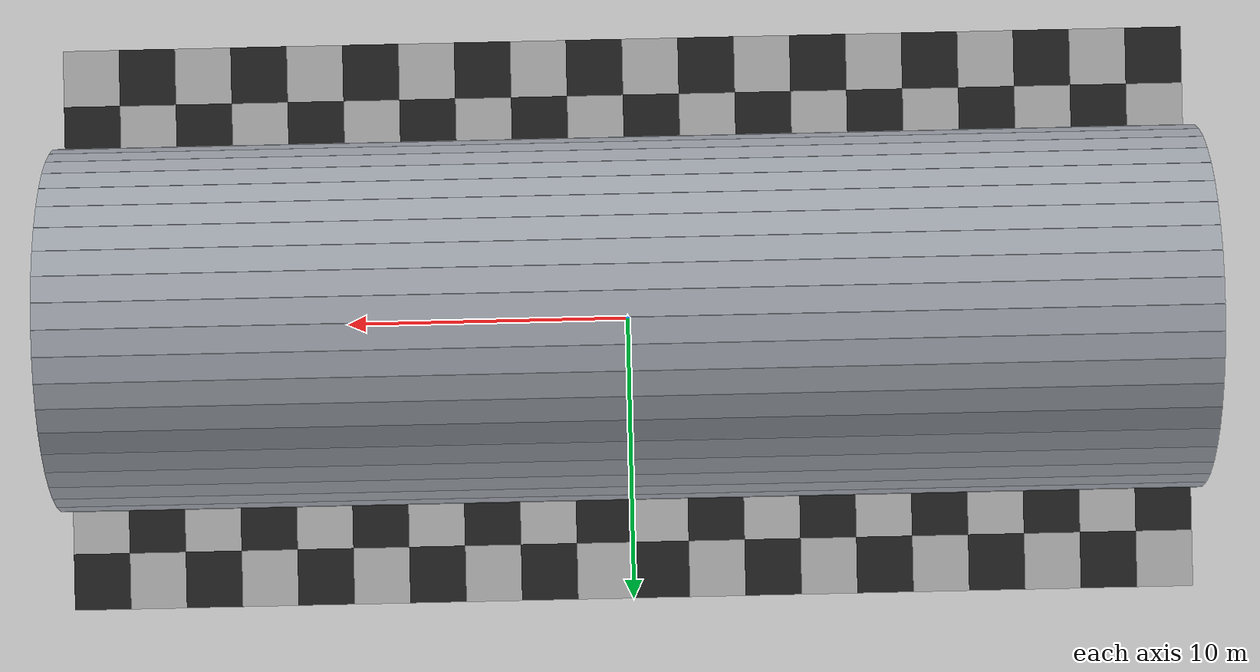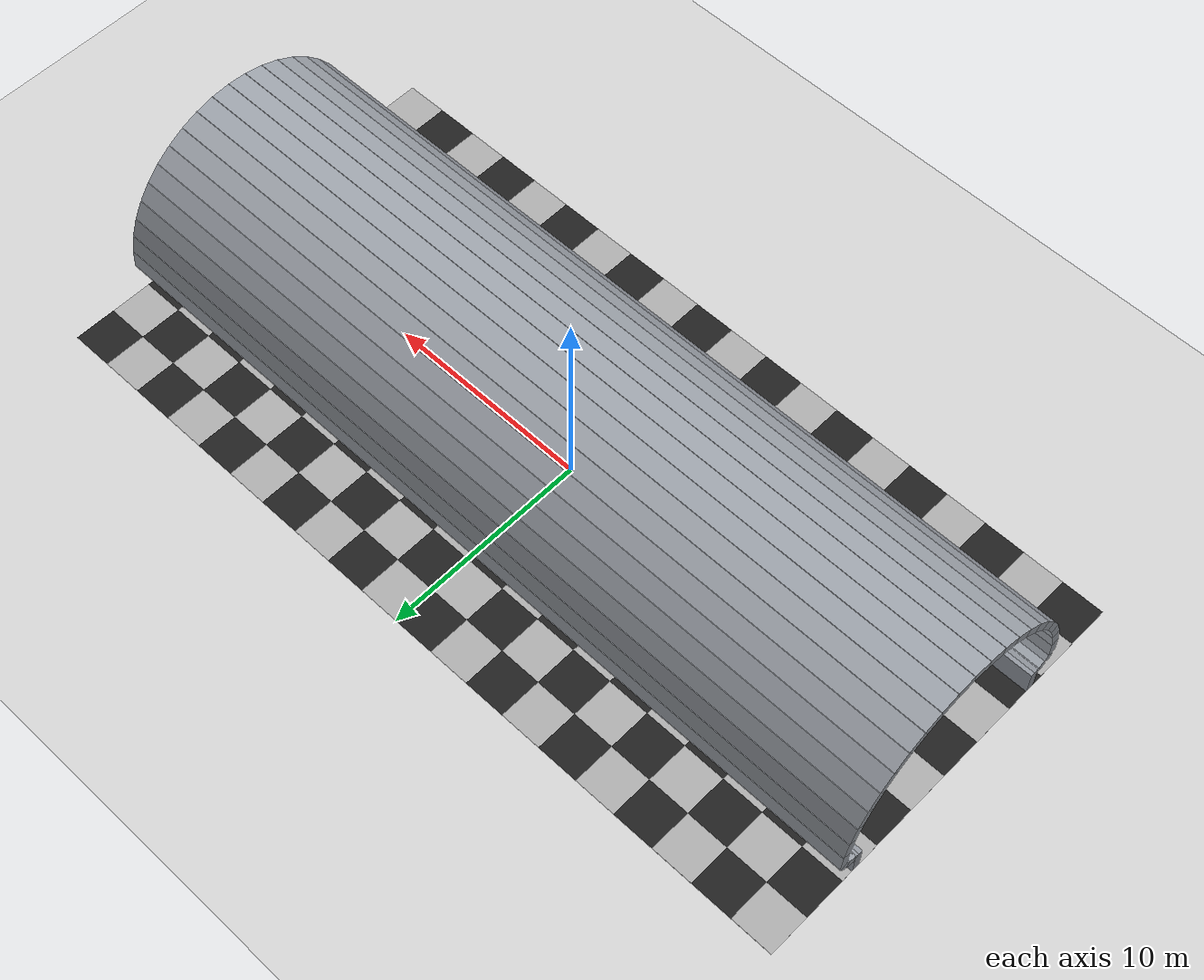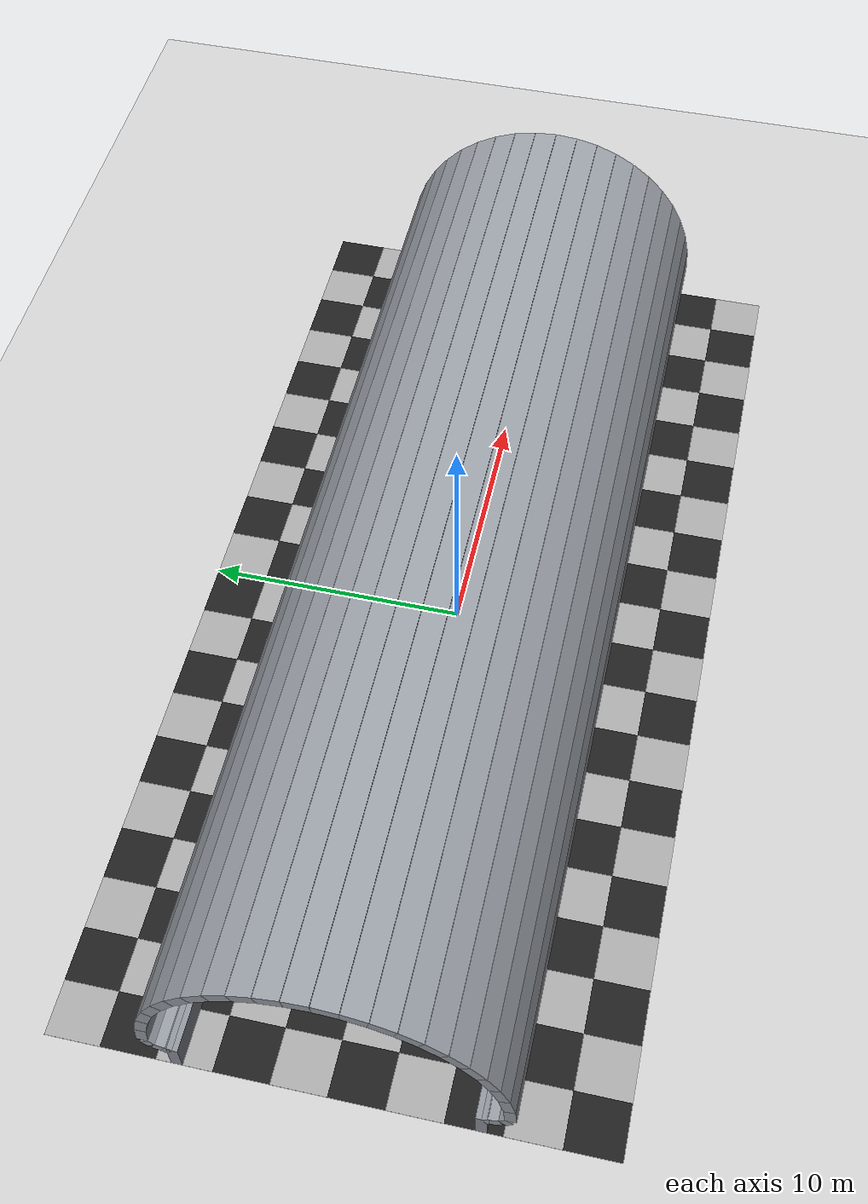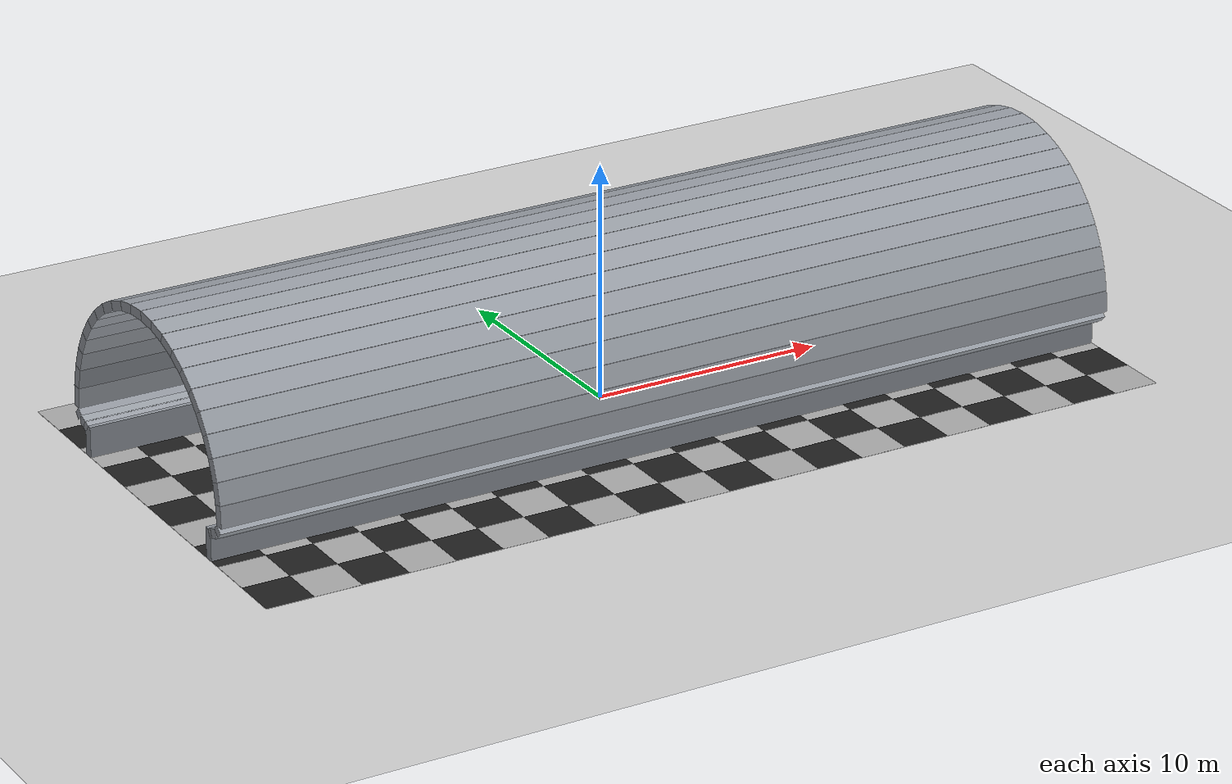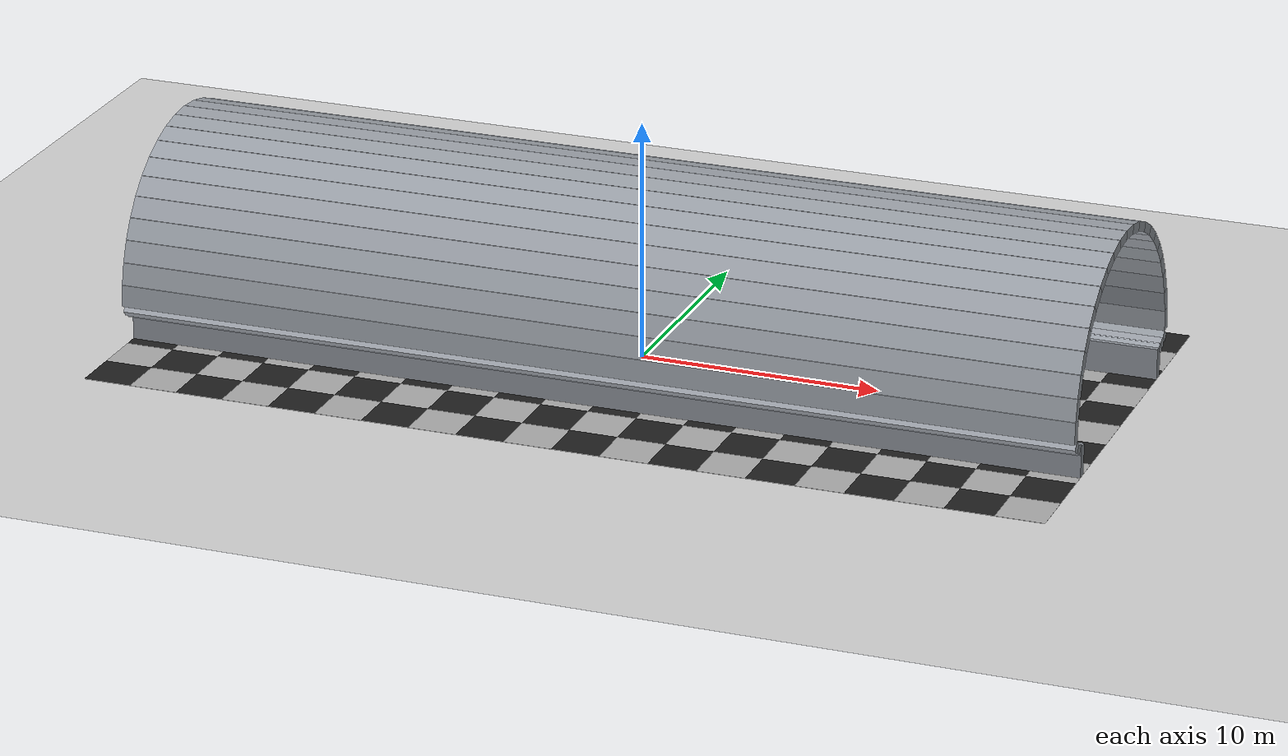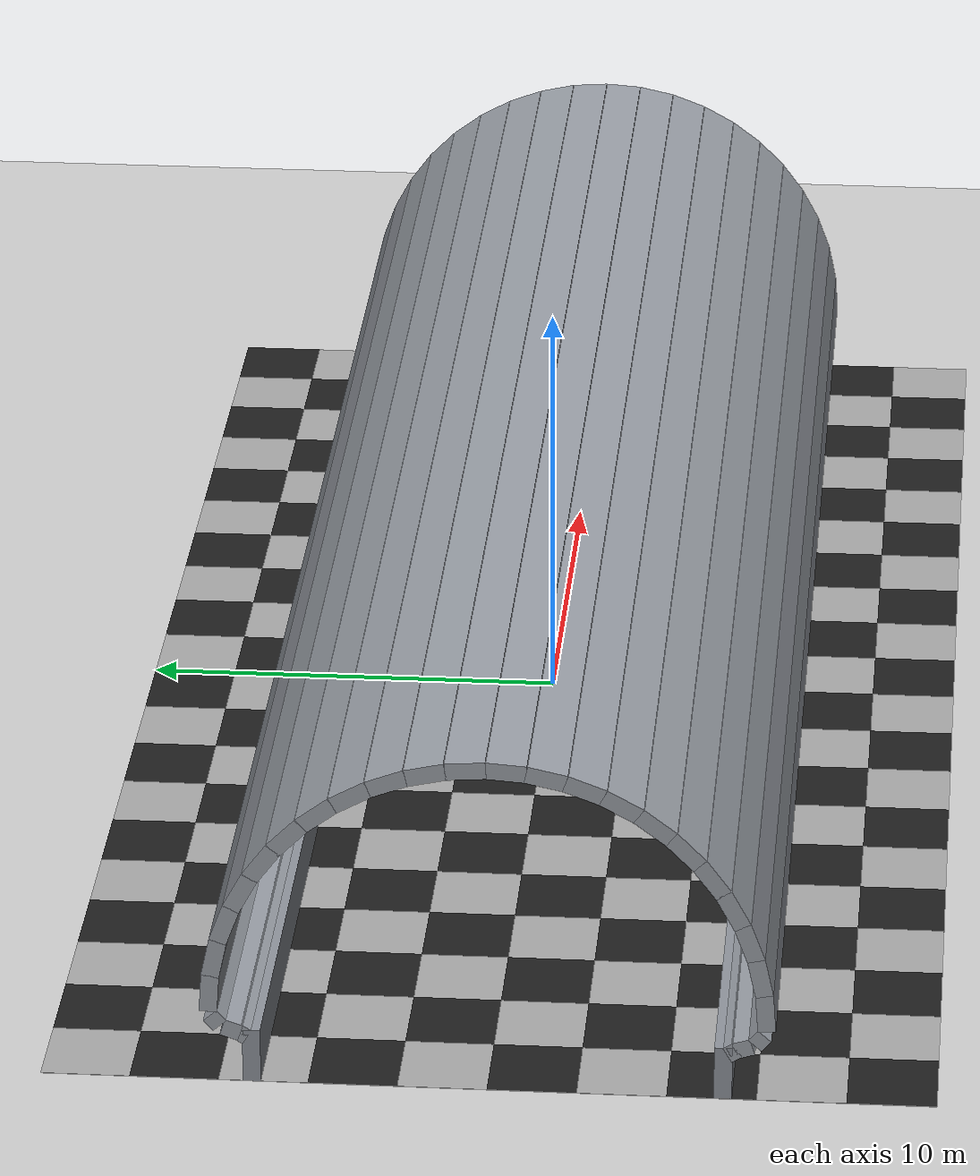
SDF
<?xml version="1.0" encoding="UTF-8"?>
<sdf version="1.9">
  <world name="v7_railway_tunnel">
    <physics type="ode"><max_step_size>0.004</max_step_size><real_time_factor>1.0</real_time_factor><real_time_update_rate>250</real_time_update_rate></physics>
    <gravity>0 0 -9.8</gravity>
    <magnetic_field>6e-06 2.3e-05 -4.2e-05</magnetic_field>
    <atmosphere type="adiabatic"/>
    <scene><grid>false</grid><ambient>0.4 0.4 0.4 1</ambient><background>0.12 0.12 0.14 1</background><shadows>true</shadows></scene>
    <model name="ground_plane"><static>true</static><link name="link">
      <collision name="collision"><geometry><plane><normal>0 0 1</normal><size>1 1</size></plane></geometry><surface><friction><ode/></friction><bounce/><contact/></surface></collision>
      <visual name="visual"><geometry><plane><normal>0 0 1</normal><size>500 500</size></plane></geometry><material><ambient>0.8 0.8 0.8 1</ambient><diffuse>0.8 0.8 0.8 1</diffuse><specular>0.1 0.1 0.1 1</specular></material></visual>
      <pose>0 0 0 0 0 0</pose>
    </link></model>
    <model name="optical_flow_floor"><static>true</static>
      <link name="tile_0_0"><pose>-19 -9 0.006 0 0 0</pose><visual name="visual"><geometry><box><size>2 2 0.01</size></box></geometry><material><ambient>0.12 0.12 0.12 1</ambient><diffuse>0.12 0.12 0.12 1</diffuse><specular>0.1 0.1 0.1 1</specular></material></visual></link>
      <link name="tile_0_1"><pose>-19 -7 0.006 0 0 0</pose><visual name="visual"><geometry><box><size>2 2 0.01</size></box></geometry><material><ambient>0.65 0.65 0.65 1</ambient><diffuse>0.65 0.65 0.65 1</diffuse><specular>0.1 0.1 0.1 1</specular></material></visual></link>
      <link name="tile_0_2"><pose>-19 -5 0.006 0 0 0</pose><visual name="visual"><geometry><box><size>2 2 0.01</size></box></geometry><material><ambient>0.12 0.12 0.12 1</ambient><diffuse>0.12 0.12 0.12 1</diffuse><specular>0.1 0.1 0.1 1</specular></material></visual></link>
      <link name="tile_0_3"><pose>-19 -3 0.006 0 0 0</pose><visual name="visual"><geometry><box><size>2 2 0.01</size></box></geometry><material><ambient>0.65 0.65 0.65 1</ambient><diffuse>0.65 0.65 0.65 1</diffuse><specular>0.1 0.1 0.1 1</specular></material></visual></link>
      <link name="tile_0_4"><pose>-19 -1 0.006 0 0 0</pose><visual name="visual"><geometry><box><size>2 2 0.01</size></box></geometry><material><ambient>0.12 0.12 0.12 1</ambient><diffuse>0.12 0.12 0.12 1</diffuse><specular>0.1 0.1 0.1 1</specular></material></visual></link>
      <link name="tile_0_5"><pose>-19 1 0.006 0 0 0</pose><visual name="visual"><geometry><box><size>2 2 0.01</size></box></geometry><material><ambient>0.65 0.65 0.65 1</ambient><diffuse>0.65 0.65 0.65 1</diffuse><specular>0.1 0.1 0.1 1</specular></material></visual></link>
      <link name="tile_0_6"><pose>-19 3 0.006 0 0 0</pose><visual name="visual"><geometry><box><size>2 2 0.01</size></box></geometry><material><ambient>0.12 0.12 0.12 1</ambient><diffuse>0.12 0.12 0.12 1</diffuse><specular>0.1 0.1 0.1 1</specular></material></visual></link>
      <link name="tile_0_7"><pose>-19 5 0.006 0 0 0</pose><visual name="visual"><geometry><box><size>2 2 0.01</size></box></geometry><material><ambient>0.65 0.65 0.65 1</ambient><diffuse>0.65 0.65 0.65 1</diffuse><specular>0.1 0.1 0.1 1</specular></material></visual></link>
      <link name="tile_0_8"><pose>-19 7 0.006 0 0 0</pose><visual name="visual"><geometry><box><size>2 2 0.01</size></box></geometry><material><ambient>0.12 0.12 0.12 1</ambient><diffuse>0.12 0.12 0.12 1</diffuse><specular>0.1 0.1 0.1 1</specular></material></visual></link>
      <link name="tile_0_9"><pose>-19 9 0.006 0 0 0</pose><visual name="visual"><geometry><box><size>2 2 0.01</size></box></geometry><material><ambient>0.65 0.65 0.65 1</ambient><diffuse>0.65 0.65 0.65 1</diffuse><specular>0.1 0.1 0.1 1</specular></material></visual></link>
      <link name="tile_1_0"><pose>-17 -9 0.006 0 0 0</pose><visual name="visual"><geometry><box><size>2 2 0.01</size></box></geometry><material><ambient>0.65 0.65 0.65 1</ambient><diffuse>0.65 0.65 0.65 1</diffuse><specular>0.1 0.1 0.1 1</specular></material></visual></link>
      <link name="tile_1_1"><pose>-17 -7 0.006 0 0 0</pose><visual name="visual"><geometry><box><size>2 2 0.01</size></box></geometry><material><ambient>0.12 0.12 0.12 1</ambient><diffuse>0.12 0.12 0.12 1</diffuse><specular>0.1 0.1 0.1 1</specular></material></visual></link>
      <link name="tile_1_2"><pose>-17 -5 0.006 0 0 0</pose><visual name="visual"><geometry><box><size>2 2 0.01</size></box></geometry><material><ambient>0.65 0.65 0.65 1</ambient><diffuse>0.65 0.65 0.65 1</diffuse><specular>0.1 0.1 0.1 1</specular></material></visual></link>
      <link name="tile_1_3"><pose>-17 -3 0.006 0 0 0</pose><visual name="visual"><geometry><box><size>2 2 0.01</size></box></geometry><material><ambient>0.12 0.12 0.12 1</ambient><diffuse>0.12 0.12 0.12 1</diffuse><specular>0.1 0.1 0.1 1</specular></material></visual></link>
      <link name="tile_1_4"><pose>-17 -1 0.006 0 0 0</pose><visual name="visual"><geometry><box><size>2 2 0.01</size></box></geometry><material><ambient>0.65 0.65 0.65 1</ambient><diffuse>0.65 0.65 0.65 1</diffuse><specular>0.1 0.1 0.1 1</specular></material></visual></link>
      <link name="tile_1_5"><pose>-17 1 0.006 0 0 0</pose><visual name="visual"><geometry><box><size>2 2 0.01</size></box></geometry><material><ambient>0.12 0.12 0.12 1</ambient><diffuse>0.12 0.12 0.12 1</diffuse><specular>0.1 0.1 0.1 1</specular></material></visual></link>
      <link name="tile_1_6"><pose>-17 3 0.006 0 0 0</pose><visual name="visual"><geometry><box><size>2 2 0.01</size></box></geometry><material><ambient>0.65 0.65 0.65 1</ambient><diffuse>0.65 0.65 0.65 1</diffuse><specular>0.1 0.1 0.1 1</specular></material></visual></link>
      <link name="tile_1_7"><pose>-17 5 0.006 0 0 0</pose><visual name="visual"><geometry><box><size>2 2 0.01</size></box></geometry><material><ambient>0.12 0.12 0.12 1</ambient><diffuse>0.12 0.12 0.12 1</diffuse><specular>0.1 0.1 0.1 1</specular></material></visual></link>
      <link name="tile_1_8"><pose>-17 7 0.006 0 0 0</pose><visual name="visual"><geometry><box><size>2 2 0.01</size></box></geometry><material><ambient>0.65 0.65 0.65 1</ambient><diffuse>0.65 0.65 0.65 1</diffuse><specular>0.1 0.1 0.1 1</specular></material></visual></link>
      <link name="tile_1_9"><pose>-17 9 0.006 0 0 0</pose><visual name="visual"><geometry><box><size>2 2 0.01</size></box></geometry><material><ambient>0.12 0.12 0.12 1</ambient><diffuse>0.12 0.12 0.12 1</diffuse><specular>0.1 0.1 0.1 1</specular></material></visual></link>
      <link name="tile_2_0"><pose>-15 -9 0.006 0 0 0</pose><visual name="visual"><geometry><box><size>2 2 0.01</size></box></geometry><material><ambient>0.12 0.12 0.12 1</ambient><diffuse>0.12 0.12 0.12 1</diffuse><specular>0.1 0.1 0.1 1</specular></material></visual></link>
      <link name="tile_2_1"><pose>-15 -7 0.006 0 0 0</pose><visual name="visual"><geometry><box><size>2 2 0.01</size></box></geometry><material><ambient>0.65 0.65 0.65 1</ambient><diffuse>0.65 0.65 0.65 1</diffuse><specular>0.1 0.1 0.1 1</specular></material></visual></link>
      <link name="tile_2_2"><pose>-15 -5 0.006 0 0 0</pose><visual name="visual"><geometry><box><size>2 2 0.01</size></box></geometry><material><ambient>0.12 0.12 0.12 1</ambient><diffuse>0.12 0.12 0.12 1</diffuse><specular>0.1 0.1 0.1 1</specular></material></visual></link>
      <link name="tile_2_3"><pose>-15 -3 0.006 0 0 0</pose><visual name="visual"><geometry><box><size>2 2 0.01</size></box></geometry><material><ambient>0.65 0.65 0.65 1</ambient><diffuse>0.65 0.65 0.65 1</diffuse><specular>0.1 0.1 0.1 1</specular></material></visual></link>
      <link name="tile_2_4"><pose>-15 -1 0.006 0 0 0</pose><visual name="visual"><geometry><box><size>2 2 0.01</size></box></geometry><material><ambient>0.12 0.12 0.12 1</ambient><diffuse>0.12 0.12 0.12 1</diffuse><specular>0.1 0.1 0.1 1</specular></material></visual></link>
      <link name="tile_2_5"><pose>-15 1 0.006 0 0 0</pose><visual name="visual"><geometry><box><size>2 2 0.01</size></box></geometry><material><ambient>0.65 0.65 0.65 1</ambient><diffuse>0.65 0.65 0.65 1</diffuse><specular>0.1 0.1 0.1 1</specular></material></visual></link>
      <link name="tile_2_6"><pose>-15 3 0.006 0 0 0</pose><visual name="visual"><geometry><box><size>2 2 0.01</size></box></geometry><material><ambient>0.12 0.12 0.12 1</ambient><diffuse>0.12 0.12 0.12 1</diffuse><specular>0.1 0.1 0.1 1</specular></material></visual></link>
      <link name="tile_2_7"><pose>-15 5 0.006 0 0 0</pose><visual name="visual"><geometry><box><size>2 2 0.01</size></box></geometry><material><ambient>0.65 0.65 0.65 1</ambient><diffuse>0.65 0.65 0.65 1</diffuse><specular>0.1 0.1 0.1 1</specular></material></visual></link>
      <link name="tile_2_8"><pose>-15 7 0.006 0 0 0</pose><visual name="visual"><geometry><box><size>2 2 0.01</size></box></geometry><material><ambient>0.12 0.12 0.12 1</ambient><diffuse>0.12 0.12 0.12 1</diffuse><specular>0.1 0.1 0.1 1</specular></material></visual></link>
      <link name="tile_2_9"><pose>-15 9 0.006 0 0 0</pose><visual name="visual"><geometry><box><size>2 2 0.01</size></box></geometry><material><ambient>0.65 0.65 0.65 1</ambient><diffuse>0.65 0.65 0.65 1</diffuse><specular>0.1 0.1 0.1 1</specular></material></visual></link>
      <link name="tile_3_0"><pose>-13 -9 0.006 0 0 0</pose><visual name="visual"><geometry><box><size>2 2 0.01</size></box></geometry><material><ambient>0.65 0.65 0.65 1</ambient><diffuse>0.65 0.65 0.65 1</diffuse><specular>0.1 0.1 0.1 1</specular></material></visual></link>
      <link name="tile_3_1"><pose>-13 -7 0.006 0 0 0</pose><visual name="visual"><geometry><box><size>2 2 0.01</size></box></geometry><material><ambient>0.12 0.12 0.12 1</ambient><diffuse>0.12 0.12 0.12 1</diffuse><specular>0.1 0.1 0.1 1</specular></material></visual></link>
      <link name="tile_3_2"><pose>-13 -5 0.006 0 0 0</pose><visual name="visual"><geometry><box><size>2 2 0.01</size></box></geometry><material><ambient>0.65 0.65 0.65 1</ambient><diffuse>0.65 0.65 0.65 1</diffuse><specular>0.1 0.1 0.1 1</specular></material></visual></link>
      <link name="tile_3_3"><pose>-13 -3 0.006 0 0 0</pose><visual name="visual"><geometry><box><size>2 2 0.01</size></box></geometry><material><ambient>0.12 0.12 0.12 1</ambient><diffuse>0.12 0.12 0.12 1</diffuse><specular>0.1 0.1 0.1 1</specular></material></visual></link>
      <link name="tile_3_4"><pose>-13 -1 0.006 0 0 0</pose><visual name="visual"><geometry><box><size>2 2 0.01</size></box></geometry><material><ambient>0.65 0.65 0.65 1</ambient><diffuse>0.65 0.65 0.65 1</diffuse><specular>0.1 0.1 0.1 1</specular></material></visual></link>
      <link name="tile_3_5"><pose>-13 1 0.006 0 0 0</pose><visual name="visual"><geometry><box><size>2 2 0.01</size></box></geometry><material><ambient>0.12 0.12 0.12 1</ambient><diffuse>0.12 0.12 0.12 1</diffuse><specular>0.1 0.1 0.1 1</specular></material></visual></link>
      <link name="tile_3_6"><pose>-13 3 0.006 0 0 0</pose><visual name="visual"><geometry><box><size>2 2 0.01</size></box></geometry><material><ambient>0.65 0.65 0.65 1</ambient><diffuse>0.65 0.65 0.65 1</diffuse><specular>0.1 0.1 0.1 1</specular></material></visual></link>
      <link name="tile_3_7"><pose>-13 5 0.006 0 0 0</pose><visual name="visual"><geometry><box><size>2 2 0.01</size></box></geometry><material><ambient>0.12 0.12 0.12 1</ambient><diffuse>0.12 0.12 0.12 1</diffuse><specular>0.1 0.1 0.1 1</specular></material></visual></link>
      <link name="tile_3_8"><pose>-13 7 0.006 0 0 0</pose><visual name="visual"><geometry><box><size>2 2 0.01</size></box></geometry><material><ambient>0.65 0.65 0.65 1</ambient><diffuse>0.65 0.65 0.65 1</diffuse><specular>0.1 0.1 0.1 1</specular></material></visual></link>
      <link name="tile_3_9"><pose>-13 9 0.006 0 0 0</pose><visual name="visual"><geometry><box><size>2 2 0.01</size></box></geometry><material><ambient>0.12 0.12 0.12 1</ambient><diffuse>0.12 0.12 0.12 1</diffuse><specular>0.1 0.1 0.1 1</specular></material></visual></link>
      <link name="tile_4_0"><pose>-11 -9 0.006 0 0 0</pose><visual name="visual"><geometry><box><size>2 2 0.01</size></box></geometry><material><ambient>0.12 0.12 0.12 1</ambient><diffuse>0.12 0.12 0.12 1</diffuse><specular>0.1 0.1 0.1 1</specular></material></visual></link>
      <link name="tile_4_1"><pose>-11 -7 0.006 0 0 0</pose><visual name="visual"><geometry><box><size>2 2 0.01</size></box></geometry><material><ambient>0.65 0.65 0.65 1</ambient><diffuse>0.65 0.65 0.65 1</diffuse><specular>0.1 0.1 0.1 1</specular></material></visual></link>
      <link name="tile_4_2"><pose>-11 -5 0.006 0 0 0</pose><visual name="visual"><geometry><box><size>2 2 0.01</size></box></geometry><material><ambient>0.12 0.12 0.12 1</ambient><diffuse>0.12 0.12 0.12 1</diffuse><specular>0.1 0.1 0.1 1</specular></material></visual></link>
      <link name="tile_4_3"><pose>-11 -3 0.006 0 0 0</pose><visual name="visual"><geometry><box><size>2 2 0.01</size></box></geometry><material><ambient>0.65 0.65 0.65 1</ambient><diffuse>0.65 0.65 0.65 1</diffuse><specular>0.1 0.1 0.1 1</specular></material></visual></link>
      <link name="tile_4_4"><pose>-11 -1 0.006 0 0 0</pose><visual name="visual"><geometry><box><size>2 2 0.01</size></box></geometry><material><ambient>0.12 0.12 0.12 1</ambient><diffuse>0.12 0.12 0.12 1</diffuse><specular>0.1 0.1 0.1 1</specular></material></visual></link>
      <link name="tile_4_5"><pose>-11 1 0.006 0 0 0</pose><visual name="visual"><geometry><box><size>2 2 0.01</size></box></geometry><material><ambient>0.65 0.65 0.65 1</ambient><diffuse>0.65 0.65 0.65 1</diffuse><specular>0.1 0.1 0.1 1</specular></material></visual></link>
      <link name="tile_4_6"><pose>-11 3 0.006 0 0 0</pose><visual name="visual"><geometry><box><size>2 2 0.01</size></box></geometry><material><ambient>0.12 0.12 0.12 1</ambient><diffuse>0.12 0.12 0.12 1</diffuse><specular>0.1 0.1 0.1 1</specular></material></visual></link>
      <link name="tile_4_7"><pose>-11 5 0.006 0 0 0</pose><visual name="visual"><geometry><box><size>2 2 0.01</size></box></geometry><material><ambient>0.65 0.65 0.65 1</ambient><diffuse>0.65 0.65 0.65 1</diffuse><specular>0.1 0.1 0.1 1</specular></material></visual></link>
      <link name="tile_4_8"><pose>-11 7 0.006 0 0 0</pose><visual name="visual"><geometry><box><size>2 2 0.01</size></box></geometry><material><ambient>0.12 0.12 0.12 1</ambient><diffuse>0.12 0.12 0.12 1</diffuse><specular>0.1 0.1 0.1 1</specular></material></visual></link>
      <link name="tile_4_9"><pose>-11 9 0.006 0 0 0</pose><visual name="visual"><geometry><box><size>2 2 0.01</size></box></geometry><material><ambient>0.65 0.65 0.65 1</ambient><diffuse>0.65 0.65 0.65 1</diffuse><specular>0.1 0.1 0.1 1</specular></material></visual></link>
      <link name="tile_5_0"><pose>-9 -9 0.006 0 0 0</pose><visual name="visual"><geometry><box><size>2 2 0.01</size></box></geometry><material><ambient>0.65 0.65 0.65 1</ambient><diffuse>0.65 0.65 0.65 1</diffuse><specular>0.1 0.1 0.1 1</specular></material></visual></link>
      <link name="tile_5_1"><pose>-9 -7 0.006 0 0 0</pose><visual name="visual"><geometry><box><size>2 2 0.01</size></box></geometry><material><ambient>0.12 0.12 0.12 1</ambient><diffuse>0.12 0.12 0.12 1</diffuse><specular>0.1 0.1 0.1 1</specular></material></visual></link>
      <link name="tile_5_2"><pose>-9 -5 0.006 0 0 0</pose><visual name="visual"><geometry><box><size>2 2 0.01</size></box></geometry><material><ambient>0.65 0.65 0.65 1</ambient><diffuse>0.65 0.65 0.65 1</diffuse><specular>0.1 0.1 0.1 1</specular></material></visual></link>
      <link name="tile_5_3"><pose>-9 -3 0.006 0 0 0</pose><visual name="visual"><geometry><box><size>2 2 0.01</size></box></geometry><material><ambient>0.12 0.12 0.12 1</ambient><diffuse>0.12 0.12 0.12 1</diffuse><specular>0.1 0.1 0.1 1</specular></material></visual></link>
      <link name="tile_5_4"><pose>-9 -1 0.006 0 0 0</pose><visual name="visual"><geometry><box><size>2 2 0.01</size></box></geometry><material><ambient>0.65 0.65 0.65 1</ambient><diffuse>0.65 0.65 0.65 1</diffuse><specular>0.1 0.1 0.1 1</specular></material></visual></link>
      <link name="tile_5_5"><pose>-9 1 0.006 0 0 0</pose><visual name="visual"><geometry><box><size>2 2 0.01</size></box></geometry><material><ambient>0.12 0.12 0.12 1</ambient><diffuse>0.12 0.12 0.12 1</diffuse><specular>0.1 0.1 0.1 1</specular></material></visual></link>
      <link name="tile_5_6"><pose>-9 3 0.006 0 0 0</pose><visual name="visual"><geometry><box><size>2 2 0.01</size></box></geometry><material><ambient>0.65 0.65 0.65 1</ambient><diffuse>0.65 0.65 0.65 1</diffuse><specular>0.1 0.1 0.1 1</specular></material></visual></link>
      <link name="tile_5_7"><pose>-9 5 0.006 0 0 0</pose><visual name="visual"><geometry><box><size>2 2 0.01</size></box></geometry><material><ambient>0.12 0.12 0.12 1</ambient><diffuse>0.12 0.12 0.12 1</diffuse><specular>0.1 0.1 0.1 1</specular></material></visual></link>
      <link name="tile_5_8"><pose>-9 7 0.006 0 0 0</pose><visual name="visual"><geometry><box><size>2 2 0.01</size></box></geometry><material><ambient>0.65 0.65 0.65 1</ambient><diffuse>0.65 0.65 0.65 1</diffuse><specular>0.1 0.1 0.1 1</specular></material></visual></link>
      <link name="tile_5_9"><pose>-9 9 0.006 0 0 0</pose><visual name="visual"><geometry><box><size>2 2 0.01</size></box></geometry><material><ambient>0.12 0.12 0.12 1</ambient><diffuse>0.12 0.12 0.12 1</diffuse><specular>0.1 0.1 0.1 1</specular></material></visual></link>
      <link name="tile_6_0"><pose>-7 -9 0.006 0 0 0</pose><visual name="visual"><geometry><box><size>2 2 0.01</size></box></geometry><material><ambient>0.12 0.12 0.12 1</ambient><diffuse>0.12 0.12 0.12 1</diffuse><specular>0.1 0.1 0.1 1</specular></material></visual></link>
      <link name="tile_6_1"><pose>-7 -7 0.006 0 0 0</pose><visual name="visual"><geometry><box><size>2 2 0.01</size></box></geometry><material><ambient>0.65 0.65 0.65 1</ambient><diffuse>0.65 0.65 0.65 1</diffuse><specular>0.1 0.1 0.1 1</specular></material></visual></link>
      <link name="tile_6_2"><pose>-7 -5 0.006 0 0 0</pose><visual name="visual"><geometry><box><size>2 2 0.01</size></box></geometry><material><ambient>0.12 0.12 0.12 1</ambient><diffuse>0.12 0.12 0.12 1</diffuse><specular>0.1 0.1 0.1 1</specular></material></visual></link>
      <link name="tile_6_3"><pose>-7 -3 0.006 0 0 0</pose><visual name="visual"><geometry><box><size>2 2 0.01</size></box></geometry><material><ambient>0.65 0.65 0.65 1</ambient><diffuse>0.65 0.65 0.65 1</diffuse><specular>0.1 0.1 0.1 1</specular></material></visual></link>
      <link name="tile_6_4"><pose>-7 -1 0.006 0 0 0</pose><visual name="visual"><geometry><box><size>2 2 0.01</size></box></geometry><material><ambient>0.12 0.12 0.12 1</ambient><diffuse>0.12 0.12 0.12 1</diffuse><specular>0.1 0.1 0.1 1</specular></material></visual></link>
      <link name="tile_6_5"><pose>-7 1 0.006 0 0 0</pose><visual name="visual"><geometry><box><size>2 2 0.01</size></box></geometry><material><ambient>0.65 0.65 0.65 1</ambient><diffuse>0.65 0.65 0.65 1</diffuse><specular>0.1 0.1 0.1 1</specular></material></visual></link>
      <link name="tile_6_6"><pose>-7 3 0.006 0 0 0</pose><visual name="visual"><geometry><box><size>2 2 0.01</size></box></geometry><material><ambient>0.12 0.12 0.12 1</ambient><diffuse>0.12 0.12 0.12 1</diffuse><specular>0.1 0.1 0.1 1</specular></material></visual></link>
      <link name="tile_6_7"><pose>-7 5 0.006 0 0 0</pose><visual name="visual"><geometry><box><size>2 2 0.01</size></box></geometry><material><ambient>0.65 0.65 0.65 1</ambient><diffuse>0.65 0.65 0.65 1</diffuse><specular>0.1 0.1 0.1 1</specular></material></visual></link>
      <link name="tile_6_8"><pose>-7 7 0.006 0 0 0</pose><visual name="visual"><geometry><box><size>2 2 0.01</size></box></geometry><material><ambient>0.12 0.12 0.12 1</ambient><diffuse>0.12 0.12 0.12 1</diffuse><specular>0.1 0.1 0.1 1</specular></material></visual></link>
      <link name="tile_6_9"><pose>-7 9 0.006 0 0 0</pose><visual name="visual"><geometry><box><size>2 2 0.01</size></box></geometry><material><ambient>0.65 0.65 0.65 1</ambient><diffuse>0.65 0.65 0.65 1</diffuse><specular>0.1 0.1 0.1 1</specular></material></visual></link>
      <link name="tile_7_0"><pose>-5 -9 0.006 0 0 0</pose><visual name="visual"><geometry><box><size>2 2 0.01</size></box></geometry><material><ambient>0.65 0.65 0.65 1</ambient><diffuse>0.65 0.65 0.65 1</diffuse><specular>0.1 0.1 0.1 1</specular></material></visual></link>
      <link name="tile_7_1"><pose>-5 -7 0.006 0 0 0</pose><visual name="visual"><geometry><box><size>2 2 0.01</size></box></geometry><material><ambient>0.12 0.12 0.12 1</ambient><diffuse>0.12 0.12 0.12 1</diffuse><specular>0.1 0.1 0.1 1</specular></material></visual></link>
      <link name="tile_7_2"><pose>-5 -5 0.006 0 0 0</pose><visual name="visual"><geometry><box><size>2 2 0.01</size></box></geometry><material><ambient>0.65 0.65 0.65 1</ambient><diffuse>0.65 0.65 0.65 1</diffuse><specular>0.1 0.1 0.1 1</specular></material></visual></link>
      <link name="tile_7_3"><pose>-5 -3 0.006 0 0 0</pose><visual name="visual"><geometry><box><size>2 2 0.01</size></box></geometry><material><ambient>0.12 0.12 0.12 1</ambient><diffuse>0.12 0.12 0.12 1</diffuse><specular>0.1 0.1 0.1 1</specular></material></visual></link>
      <link name="tile_7_4"><pose>-5 -1 0.006 0 0 0</pose><visual name="visual"><geometry><box><size>2 2 0.01</size></box></geometry><material><ambient>0.65 0.65 0.65 1</ambient><diffuse>0.65 0.65 0.65 1</diffuse><specular>0.1 0.1 0.1 1</specular></material></visual></link>
      <link name="tile_7_5"><pose>-5 1 0.006 0 0 0</pose><visual name="visual"><geometry><box><size>2 2 0.01</size></box></geometry><material><ambient>0.12 0.12 0.12 1</ambient><diffuse>0.12 0.12 0.12 1</diffuse><specular>0.1 0.1 0.1 1</specular></material></visual></link>
      <link name="tile_7_6"><pose>-5 3 0.006 0 0 0</pose><visual name="visual"><geometry><box><size>2 2 0.01</size></box></geometry><material><ambient>0.65 0.65 0.65 1</ambient><diffuse>0.65 0.65 0.65 1</diffuse><specular>0.1 0.1 0.1 1</specular></material></visual></link>
      <link name="tile_7_7"><pose>-5 5 0.006 0 0 0</pose><visual name="visual"><geometry><box><size>2 2 0.01</size></box></geometry><material><ambient>0.12 0.12 0.12 1</ambient><diffuse>0.12 0.12 0.12 1</diffuse><specular>0.1 0.1 0.1 1</specular></material></visual></link>
      <link name="tile_7_8"><pose>-5 7 0.006 0 0 0</pose><visual name="visual"><geometry><box><size>2 2 0.01</size></box></geometry><material><ambient>0.65 0.65 0.65 1</ambient><diffuse>0.65 0.65 0.65 1</diffuse><specular>0.1 0.1 0.1 1</specular></material></visual></link>
      <link name="tile_7_9"><pose>-5 9 0.006 0 0 0</pose><visual name="visual"><geometry><box><size>2 2 0.01</size></box></geometry><material><ambient>0.12 0.12 0.12 1</ambient><diffuse>0.12 0.12 0.12 1</diffuse><specular>0.1 0.1 0.1 1</specular></material></visual></link>
      <link name="tile_8_0"><pose>-3 -9 0.006 0 0 0</pose><visual name="visual"><geometry><box><size>2 2 0.01</size></box></geometry><material><ambient>0.12 0.12 0.12 1</ambient><diffuse>0.12 0.12 0.12 1</diffuse><specular>0.1 0.1 0.1 1</specular></material></visual></link>
      <link name="tile_8_1"><pose>-3 -7 0.006 0 0 0</pose><visual name="visual"><geometry><box><size>2 2 0.01</size></box></geometry><material><ambient>0.65 0.65 0.65 1</ambient><diffuse>0.65 0.65 0.65 1</diffuse><specular>0.1 0.1 0.1 1</specular></material></visual></link>
      <link name="tile_8_2"><pose>-3 -5 0.006 0 0 0</pose><visual name="visual"><geometry><box><size>2 2 0.01</size></box></geometry><material><ambient>0.12 0.12 0.12 1</ambient><diffuse>0.12 0.12 0.12 1</diffuse><specular>0.1 0.1 0.1 1</specular></material></visual></link>
      <link name="tile_8_3"><pose>-3 -3 0.006 0 0 0</pose><visual name="visual"><geometry><box><size>2 2 0.01</size></box></geometry><material><ambient>0.65 0.65 0.65 1</ambient><diffuse>0.65 0.65 0.65 1</diffuse><specular>0.1 0.1 0.1 1</specular></material></visual></link>
      <link name="tile_8_4"><pose>-3 -1 0.006 0 0 0</pose><visual name="visual"><geometry><box><size>2 2 0.01</size></box></geometry><material><ambient>0.12 0.12 0.12 1</ambient><diffuse>0.12 0.12 0.12 1</diffuse><specular>0.1 0.1 0.1 1</specular></material></visual></link>
      <link name="tile_8_5"><pose>-3 1 0.006 0 0 0</pose><visual name="visual"><geometry><box><size>2 2 0.01</size></box></geometry><material><ambient>0.65 0.65 0.65 1</ambient><diffuse>0.65 0.65 0.65 1</diffuse><specular>0.1 0.1 0.1 1</specular></material></visual></link>
      <link name="tile_8_6"><pose>-3 3 0.006 0 0 0</pose><visual name="visual"><geometry><box><size>2 2 0.01</size></box></geometry><material><ambient>0.12 0.12 0.12 1</ambient><diffuse>0.12 0.12 0.12 1</diffuse><specular>0.1 0.1 0.1 1</specular></material></visual></link>
      <link name="tile_8_7"><pose>-3 5 0.006 0 0 0</pose><visual name="visual"><geometry><box><size>2 2 0.01</size></box></geometry><material><ambient>0.65 0.65 0.65 1</ambient><diffuse>0.65 0.65 0.65 1</diffuse><specular>0.1 0.1 0.1 1</specular></material></visual></link>
      <link name="tile_8_8"><pose>-3 7 0.006 0 0 0</pose><visual name="visual"><geometry><box><size>2 2 0.01</size></box></geometry><material><ambient>0.12 0.12 0.12 1</ambient><diffuse>0.12 0.12 0.12 1</diffuse><specular>0.1 0.1 0.1 1</specular></material></visual></link>
      <link name="tile_8_9"><pose>-3 9 0.006 0 0 0</pose><visual name="visual"><geometry><box><size>2 2 0.01</size></box></geometry><material><ambient>0.65 0.65 0.65 1</ambient><diffuse>0.65 0.65 0.65 1</diffuse><specular>0.1 0.1 0.1 1</specular></material></visual></link>
      <link name="tile_9_0"><pose>-1 -9 0.006 0 0 0</pose><visual name="visual"><geometry><box><size>2 2 0.01</size></box></geometry><material><ambient>0.65 0.65 0.65 1</ambient><diffuse>0.65 0.65 0.65 1</diffuse><specular>0.1 0.1 0.1 1</specular></material></visual></link>
      <link name="tile_9_1"><pose>-1 -7 0.006 0 0 0</pose><visual name="visual"><geometry><box><size>2 2 0.01</size></box></geometry><material><ambient>0.12 0.12 0.12 1</ambient><diffuse>0.12 0.12 0.12 1</diffuse><specular>0.1 0.1 0.1 1</specular></material></visual></link>
      <link name="tile_9_2"><pose>-1 -5 0.006 0 0 0</pose><visual name="visual"><geometry><box><size>2 2 0.01</size></box></geometry><material><ambient>0.65 0.65 0.65 1</ambient><diffuse>0.65 0.65 0.65 1</diffuse><specular>0.1 0.1 0.1 1</specular></material></visual></link>
      <link name="tile_9_3"><pose>-1 -3 0.006 0 0 0</pose><visual name="visual"><geometry><box><size>2 2 0.01</size></box></geometry><material><ambient>0.12 0.12 0.12 1</ambient><diffuse>0.12 0.12 0.12 1</diffuse><specular>0.1 0.1 0.1 1</specular></material></visual></link>
      <link name="tile_9_4"><pose>-1 -1 0.006 0 0 0</pose><visual name="visual"><geometry><box><size>2 2 0.01</size></box></geometry><material><ambient>0.65 0.65 0.65 1</ambient><diffuse>0.65 0.65 0.65 1</diffuse><specular>0.1 0.1 0.1 1</specular></material></visual></link>
      <link name="tile_9_5"><pose>-1 1 0.006 0 0 0</pose><visual name="visual"><geometry><box><size>2 2 0.01</size></box></geometry><material><ambient>0.12 0.12 0.12 1</ambient><diffuse>0.12 0.12 0.12 1</diffuse><specular>0.1 0.1 0.1 1</specular></material></visual></link>
      <link name="tile_9_6"><pose>-1 3 0.006 0 0 0</pose><visual name="visual"><geometry><box><size>2 2 0.01</size></box></geometry><material><ambient>0.65 0.65 0.65 1</ambient><diffuse>0.65 0.65 0.65 1</diffuse><specular>0.1 0.1 0.1 1</specular></material></visual></link>
      <link name="tile_9_7"><pose>-1 5 0.006 0 0 0</pose><visual name="visual"><geometry><box><size>2 2 0.01</size></box></geometry><material><ambient>0.12 0.12 0.12 1</ambient><diffuse>0.12 0.12 0.12 1</diffuse><specular>0.1 0.1 0.1 1</specular></material></visual></link>
      <link name="tile_9_8"><pose>-1 7 0.006 0 0 0</pose><visual name="visual"><geometry><box><size>2 2 0.01</size></box></geometry><material><ambient>0.65 0.65 0.65 1</ambient><diffuse>0.65 0.65 0.65 1</diffuse><specular>0.1 0.1 0.1 1</specular></material></visual></link>
      <link name="tile_9_9"><pose>-1 9 0.006 0 0 0</pose><visual name="visual"><geometry><box><size>2 2 0.01</size></box></geometry><material><ambient>0.12 0.12 0.12 1</ambient><diffuse>0.12 0.12 0.12 1</diffuse><specular>0.1 0.1 0.1 1</specular></material></visual></link>
      <link name="tile_10_0"><pose>1 -9 0.006 0 0 0</pose><visual name="visual"><geometry><box><size>2 2 0.01</size></box></geometry><material><ambient>0.12 0.12 0.12 1</ambient><diffuse>0.12 0.12 0.12 1</diffuse><specular>0.1 0.1 0.1 1</specular></material></visual></link>
      <link name="tile_10_1"><pose>1 -7 0.006 0 0 0</pose><visual name="visual"><geometry><box><size>2 2 0.01</size></box></geometry><material><ambient>0.65 0.65 0.65 1</ambient><diffuse>0.65 0.65 0.65 1</diffuse><specular>0.1 0.1 0.1 1</specular></material></visual></link>
      <link name="tile_10_2"><pose>1 -5 0.006 0 0 0</pose><visual name="visual"><geometry><box><size>2 2 0.01</size></box></geometry><material><ambient>0.12 0.12 0.12 1</ambient><diffuse>0.12 0.12 0.12 1</diffuse><specular>0.1 0.1 0.1 1</specular></material></visual></link>
      <link name="tile_10_3"><pose>1 -3 0.006 0 0 0</pose><visual name="visual"><geometry><box><size>2 2 0.01</size></box></geometry><material><ambient>0.65 0.65 0.65 1</ambient><diffuse>0.65 0.65 0.65 1</diffuse><specular>0.1 0.1 0.1 1</specular></material></visual></link>
      <link name="tile_10_4"><pose>1 -1 0.006 0 0 0</pose><visual name="visual"><geometry><box><size>2 2 0.01</size></box></geometry><material><ambient>0.12 0.12 0.12 1</ambient><diffuse>0.12 0.12 0.12 1</diffuse><specular>0.1 0.1 0.1 1</specular></material></visual></link>
      <link name="tile_10_5"><pose>1 1 0.006 0 0 0</pose><visual name="visual"><geometry><box><size>2 2 0.01</size></box></geometry><material><ambient>0.65 0.65 0.65 1</ambient><diffuse>0.65 0.65 0.65 1</diffuse><specular>0.1 0.1 0.1 1</specular></material></visual></link>
      <link name="tile_10_6"><pose>1 3 0.006 0 0 0</pose><visual name="visual"><geometry><box><size>2 2 0.01</size></box></geometry><material><ambient>0.12 0.12 0.12 1</ambient><diffuse>0.12 0.12 0.12 1</diffuse><specular>0.1 0.1 0.1 1</specular></material></visual></link>
      <link name="tile_10_7"><pose>1 5 0.006 0 0 0</pose><visual name="visual"><geometry><box><size>2 2 0.01</size></box></geometry><material><ambient>0.65 0.65 0.65 1</ambient><diffuse>0.65 0.65 0.65 1</diffuse><specular>0.1 0.1 0.1 1</specular></material></visual></link>
      <link name="tile_10_8"><pose>1 7 0.006 0 0 0</pose><visual name="visual"><geometry><box><size>2 2 0.01</size></box></geometry><material><ambient>0.12 0.12 0.12 1</ambient><diffuse>0.12 0.12 0.12 1</diffuse><specular>0.1 0.1 0.1 1</specular></material></visual></link>
      <link name="tile_10_9"><pose>1 9 0.006 0 0 0</pose><visual name="visual"><geometry><box><size>2 2 0.01</size></box></geometry><material><ambient>0.65 0.65 0.65 1</ambient><diffuse>0.65 0.65 0.65 1</diffuse><specular>0.1 0.1 0.1 1</specular></material></visual></link>
      <link name="tile_11_0"><pose>3 -9 0.006 0 0 0</pose><visual name="visual"><geometry><box><size>2 2 0.01</size></box></geometry><material><ambient>0.65 0.65 0.65 1</ambient><diffuse>0.65 0.65 0.65 1</diffuse><specular>0.1 0.1 0.1 1</specular></material></visual></link>
      <link name="tile_11_1"><pose>3 -7 0.006 0 0 0</pose><visual name="visual"><geometry><box><size>2 2 0.01</size></box></geometry><material><ambient>0.12 0.12 0.12 1</ambient><diffuse>0.12 0.12 0.12 1</diffuse><specular>0.1 0.1 0.1 1</specular></material></visual></link>
      <link name="tile_11_2"><pose>3 -5 0.006 0 0 0</pose><visual name="visual"><geometry><box><size>2 2 0.01</size></box></geometry><material><ambient>0.65 0.65 0.65 1</ambient><diffuse>0.65 0.65 0.65 1</diffuse><specular>0.1 0.1 0.1 1</specular></material></visual></link>
      <link name="tile_11_3"><pose>3 -3 0.006 0 0 0</pose><visual name="visual"><geometry><box><size>2 2 0.01</size></box></geometry><material><ambient>0.12 0.12 0.12 1</ambient><diffuse>0.12 0.12 0.12 1</diffuse><specular>0.1 0.1 0.1 1</specular></material></visual></link>
      <link name="tile_11_4"><pose>3 -1 0.006 0 0 0</pose><visual name="visual"><geometry><box><size>2 2 0.01</size></box></geometry><material><ambient>0.65 0.65 0.65 1</ambient><diffuse>0.65 0.65 0.65 1</diffuse><specular>0.1 0.1 0.1 1</specular></material></visual></link>
      <link name="tile_11_5"><pose>3 1 0.006 0 0 0</pose><visual name="visual"><geometry><box><size>2 2 0.01</size></box></geometry><material><ambient>0.12 0.12 0.12 1</ambient><diffuse>0.12 0.12 0.12 1</diffuse><specular>0.1 0.1 0.1 1</specular></material></visual></link>
      <link name="tile_11_6"><pose>3 3 0.006 0 0 0</pose><visual name="visual"><geometry><box><size>2 2 0.01</size></box></geometry><material><ambient>0.65 0.65 0.65 1</ambient><diffuse>0.65 0.65 0.65 1</diffuse><specular>0.1 0.1 0.1 1</specular></material></visual></link>
      <link name="tile_11_7"><pose>3 5 0.006 0 0 0</pose><visual name="visual"><geometry><box><size>2 2 0.01</size></box></geometry><material><ambient>0.12 0.12 0.12 1</ambient><diffuse>0.12 0.12 0.12 1</diffuse><specular>0.1 0.1 0.1 1</specular></material></visual></link>
      <link name="tile_11_8"><pose>3 7 0.006 0 0 0</pose><visual name="visual"><geometry><box><size>2 2 0.01</size></box></geometry><material><ambient>0.65 0.65 0.65 1</ambient><diffuse>0.65 0.65 0.65 1</diffuse><specular>0.1 0.1 0.1 1</specular></material></visual></link>
      <link name="tile_11_9"><pose>3 9 0.006 0 0 0</pose><visual name="visual"><geometry><box><size>2 2 0.01</size></box></geometry><material><ambient>0.12 0.12 0.12 1</ambient><diffuse>0.12 0.12 0.12 1</diffuse><specular>0.1 0.1 0.1 1</specular></material></visual></link>
      <link name="tile_12_0"><pose>5 -9 0.006 0 0 0</pose><visual name="visual"><geometry><box><size>2 2 0.01</size></box></geometry><material><ambient>0.12 0.12 0.12 1</ambient><diffuse>0.12 0.12 0.12 1</diffuse><specular>0.1 0.1 0.1 1</specular></material></visual></link>
      <link name="tile_12_1"><pose>5 -7 0.006 0 0 0</pose><visual name="visual"><geometry><box><size>2 2 0.01</size></box></geometry><material><ambient>0.65 0.65 0.65 1</ambient><diffuse>0.65 0.65 0.65 1</diffuse><specular>0.1 0.1 0.1 1</specular></material></visual></link>
      <link name="tile_12_2"><pose>5 -5 0.006 0 0 0</pose><visual name="visual"><geometry><box><size>2 2 0.01</size></box></geometry><material><ambient>0.12 0.12 0.12 1</ambient><diffuse>0.12 0.12 0.12 1</diffuse><specular>0.1 0.1 0.1 1</specular></material></visual></link>
      <link name="tile_12_3"><pose>5 -3 0.006 0 0 0</pose><visual name="visual"><geometry><box><size>2 2 0.01</size></box></geometry><material><ambient>0.65 0.65 0.65 1</ambient><diffuse>0.65 0.65 0.65 1</diffuse><specular>0.1 0.1 0.1 1</specular></material></visual></link>
      <link name="tile_12_4"><pose>5 -1 0.006 0 0 0</pose><visual name="visual"><geometry><box><size>2 2 0.01</size></box></geometry><material><ambient>0.12 0.12 0.12 1</ambient><diffuse>0.12 0.12 0.12 1</diffuse><specular>0.1 0.1 0.1 1</specular></material></visual></link>
      <link name="tile_12_5"><pose>5 1 0.006 0 0 0</pose><visual name="visual"><geometry><box><size>2 2 0.01</size></box></geometry><material><ambient>0.65 0.65 0.65 1</ambient><diffuse>0.65 0.65 0.65 1</diffuse><specular>0.1 0.1 0.1 1</specular></material></visual></link>
      <link name="tile_12_6"><pose>5 3 0.006 0 0 0</pose><visual name="visual"><geometry><box><size>2 2 0.01</size></box></geometry><material><ambient>0.12 0.12 0.12 1</ambient><diffuse>0.12 0.12 0.12 1</diffuse><specular>0.1 0.1 0.1 1</specular></material></visual></link>
      <link name="tile_12_7"><pose>5 5 0.006 0 0 0</pose><visual name="visual"><geometry><box><size>2 2 0.01</size></box></geometry><material><ambient>0.65 0.65 0.65 1</ambient><diffuse>0.65 0.65 0.65 1</diffuse><specular>0.1 0.1 0.1 1</specular></material></visual></link>
      <link name="tile_12_8"><pose>5 7 0.006 0 0 0</pose><visual name="visual"><geometry><box><size>2 2 0.01</size></box></geometry><material><ambient>0.12 0.12 0.12 1</ambient><diffuse>0.12 0.12 0.12 1</diffuse><specular>0.1 0.1 0.1 1</specular></material></visual></link>
      <link name="tile_12_9"><pose>5 9 0.006 0 0 0</pose><visual name="visual"><geometry><box><size>2 2 0.01</size></box></geometry><material><ambient>0.65 0.65 0.65 1</ambient><diffuse>0.65 0.65 0.65 1</diffuse><specular>0.1 0.1 0.1 1</specular></material></visual></link>
      <link name="tile_13_0"><pose>7 -9 0.006 0 0 0</pose><visual name="visual"><geometry><box><size>2 2 0.01</size></box></geometry><material><ambient>0.65 0.65 0.65 1</ambient><diffuse>0.65 0.65 0.65 1</diffuse><specular>0.1 0.1 0.1 1</specular></material></visual></link>
      <link name="tile_13_1"><pose>7 -7 0.006 0 0 0</pose><visual name="visual"><geometry><box><size>2 2 0.01</size></box></geometry><material><ambient>0.12 0.12 0.12 1</ambient><diffuse>0.12 0.12 0.12 1</diffuse><specular>0.1 0.1 0.1 1</specular></material></visual></link>
      <link name="tile_13_2"><pose>7 -5 0.006 0 0 0</pose><visual name="visual"><geometry><box><size>2 2 0.01</size></box></geometry><material><ambient>0.65 0.65 0.65 1</ambient><diffuse>0.65 0.65 0.65 1</diffuse><specular>0.1 0.1 0.1 1</specular></material></visual></link>
      <link name="tile_13_3"><pose>7 -3 0.006 0 0 0</pose><visual name="visual"><geometry><box><size>2 2 0.01</size></box></geometry><material><ambient>0.12 0.12 0.12 1</ambient><diffuse>0.12 0.12 0.12 1</diffuse><specular>0.1 0.1 0.1 1</specular></material></visual></link>
      <link name="tile_13_4"><pose>7 -1 0.006 0 0 0</pose><visual name="visual"><geometry><box><size>2 2 0.01</size></box></geometry><material><ambient>0.65 0.65 0.65 1</ambient><diffuse>0.65 0.65 0.65 1</diffuse><specular>0.1 0.1 0.1 1</specular></material></visual></link>
      <link name="tile_13_5"><pose>7 1 0.006 0 0 0</pose><visual name="visual"><geometry><box><size>2 2 0.01</size></box></geometry><material><ambient>0.12 0.12 0.12 1</ambient><diffuse>0.12 0.12 0.12 1</diffuse><specular>0.1 0.1 0.1 1</specular></material></visual></link>
      <link name="tile_13_6"><pose>7 3 0.006 0 0 0</pose><visual name="visual"><geometry><box><size>2 2 0.01</size></box></geometry><material><ambient>0.65 0.65 0.65 1</ambient><diffuse>0.65 0.65 0.65 1</diffuse><specular>0.1 0.1 0.1 1</specular></material></visual></link>
      <link name="tile_13_7"><pose>7 5 0.006 0 0 0</pose><visual name="visual"><geometry><box><size>2 2 0.01</size></box></geometry><material><ambient>0.12 0.12 0.12 1</ambient><diffuse>0.12 0.12 0.12 1</diffuse><specular>0.1 0.1 0.1 1</specular></material></visual></link>
      <link name="tile_13_8"><pose>7 7 0.006 0 0 0</pose><visual name="visual"><geometry><box><size>2 2 0.01</size></box></geometry><material><ambient>0.65 0.65 0.65 1</ambient><diffuse>0.65 0.65 0.65 1</diffuse><specular>0.1 0.1 0.1 1</specular></material></visual></link>
      <link name="tile_13_9"><pose>7 9 0.006 0 0 0</pose><visual name="visual"><geometry><box><size>2 2 0.01</size></box></geometry><material><ambient>0.12 0.12 0.12 1</ambient><diffuse>0.12 0.12 0.12 1</diffuse><specular>0.1 0.1 0.1 1</specular></material></visual></link>
      <link name="tile_14_0"><pose>9 -9 0.006 0 0 0</pose><visual name="visual"><geometry><box><size>2 2 0.01</size></box></geometry><material><ambient>0.12 0.12 0.12 1</ambient><diffuse>0.12 0.12 0.12 1</diffuse><specular>0.1 0.1 0.1 1</specular></material></visual></link>
      <link name="tile_14_1"><pose>9 -7 0.006 0 0 0</pose><visual name="visual"><geometry><box><size>2 2 0.01</size></box></geometry><material><ambient>0.65 0.65 0.65 1</ambient><diffuse>0.65 0.65 0.65 1</diffuse><specular>0.1 0.1 0.1 1</specular></material></visual></link>
      <link name="tile_14_2"><pose>9 -5 0.006 0 0 0</pose><visual name="visual"><geometry><box><size>2 2 0.01</size></box></geometry><material><ambient>0.12 0.12 0.12 1</ambient><diffuse>0.12 0.12 0.12 1</diffuse><specular>0.1 0.1 0.1 1</specular></material></visual></link>
      <link name="tile_14_3"><pose>9 -3 0.006 0 0 0</pose><visual name="visual"><geometry><box><size>2 2 0.01</size></box></geometry><material><ambient>0.65 0.65 0.65 1</ambient><diffuse>0.65 0.65 0.65 1</diffuse><specular>0.1 0.1 0.1 1</specular></material></visual></link>
      <link name="tile_14_4"><pose>9 -1 0.006 0 0 0</pose><visual name="visual"><geometry><box><size>2 2 0.01</size></box></geometry><material><ambient>0.12 0.12 0.12 1</ambient><diffuse>0.12 0.12 0.12 1</diffuse><specular>0.1 0.1 0.1 1</specular></material></visual></link>
      <link name="tile_14_5"><pose>9 1 0.006 0 0 0</pose><visual name="visual"><geometry><box><size>2 2 0.01</size></box></geometry><material><ambient>0.65 0.65 0.65 1</ambient><diffuse>0.65 0.65 0.65 1</diffuse><specular>0.1 0.1 0.1 1</specular></material></visual></link>
      <link name="tile_14_6"><pose>9 3 0.006 0 0 0</pose><visual name="visual"><geometry><box><size>2 2 0.01</size></box></geometry><material><ambient>0.12 0.12 0.12 1</ambient><diffuse>0.12 0.12 0.12 1</diffuse><specular>0.1 0.1 0.1 1</specular></material></visual></link>
      <link name="tile_14_7"><pose>9 5 0.006 0 0 0</pose><visual name="visual"><geometry><box><size>2 2 0.01</size></box></geometry><material><ambient>0.65 0.65 0.65 1</ambient><diffuse>0.65 0.65 0.65 1</diffuse><specular>0.1 0.1 0.1 1</specular></material></visual></link>
      <link name="tile_14_8"><pose>9 7 0.006 0 0 0</pose><visual name="visual"><geometry><box><size>2 2 0.01</size></box></geometry><material><ambient>0.12 0.12 0.12 1</ambient><diffuse>0.12 0.12 0.12 1</diffuse><specular>0.1 0.1 0.1 1</specular></material></visual></link>
      <link name="tile_14_9"><pose>9 9 0.006 0 0 0</pose><visual name="visual"><geometry><box><size>2 2 0.01</size></box></geometry><material><ambient>0.65 0.65 0.65 1</ambient><diffuse>0.65 0.65 0.65 1</diffuse><specular>0.1 0.1 0.1 1</specular></material></visual></link>
      <link name="tile_15_0"><pose>11 -9 0.006 0 0 0</pose><visual name="visual"><geometry><box><size>2 2 0.01</size></box></geometry><material><ambient>0.65 0.65 0.65 1</ambient><diffuse>0.65 0.65 0.65 1</diffuse><specular>0.1 0.1 0.1 1</specular></material></visual></link>
      <link name="tile_15_1"><pose>11 -7 0.006 0 0 0</pose><visual name="visual"><geometry><box><size>2 2 0.01</size></box></geometry><material><ambient>0.12 0.12 0.12 1</ambient><diffuse>0.12 0.12 0.12 1</diffuse><specular>0.1 0.1 0.1 1</specular></material></visual></link>
      <link name="tile_15_2"><pose>11 -5 0.006 0 0 0</pose><visual name="visual"><geometry><box><size>2 2 0.01</size></box></geometry><material><ambient>0.65 0.65 0.65 1</ambient><diffuse>0.65 0.65 0.65 1</diffuse><specular>0.1 0.1 0.1 1</specular></material></visual></link>
      <link name="tile_15_3"><pose>11 -3 0.006 0 0 0</pose><visual name="visual"><geometry><box><size>2 2 0.01</size></box></geometry><material><ambient>0.12 0.12 0.12 1</ambient><diffuse>0.12 0.12 0.12 1</diffuse><specular>0.1 0.1 0.1 1</specular></material></visual></link>
      <link name="tile_15_4"><pose>11 -1 0.006 0 0 0</pose><visual name="visual"><geometry><box><size>2 2 0.01</size></box></geometry><material><ambient>0.65 0.65 0.65 1</ambient><diffuse>0.65 0.65 0.65 1</diffuse><specular>0.1 0.1 0.1 1</specular></material></visual></link>
      <link name="tile_15_5"><pose>11 1 0.006 0 0 0</pose><visual name="visual"><geometry><box><size>2 2 0.01</size></box></geometry><material><ambient>0.12 0.12 0.12 1</ambient><diffuse>0.12 0.12 0.12 1</diffuse><specular>0.1 0.1 0.1 1</specular></material></visual></link>
      <link name="tile_15_6"><pose>11 3 0.006 0 0 0</pose><visual name="visual"><geometry><box><size>2 2 0.01</size></box></geometry><material><ambient>0.65 0.65 0.65 1</ambient><diffuse>0.65 0.65 0.65 1</diffuse><specular>0.1 0.1 0.1 1</specular></material></visual></link>
      <link name="tile_15_7"><pose>11 5 0.006 0 0 0</pose><visual name="visual"><geometry><box><size>2 2 0.01</size></box></geometry><material><ambient>0.12 0.12 0.12 1</ambient><diffuse>0.12 0.12 0.12 1</diffuse><specular>0.1 0.1 0.1 1</specular></material></visual></link>
      <link name="tile_15_8"><pose>11 7 0.006 0 0 0</pose><visual name="visual"><geometry><box><size>2 2 0.01</size></box></geometry><material><ambient>0.65 0.65 0.65 1</ambient><diffuse>0.65 0.65 0.65 1</diffuse><specular>0.1 0.1 0.1 1</specular></material></visual></link>
      <link name="tile_15_9"><pose>11 9 0.006 0 0 0</pose><visual name="visual"><geometry><box><size>2 2 0.01</size></box></geometry><material><ambient>0.12 0.12 0.12 1</ambient><diffuse>0.12 0.12 0.12 1</diffuse><specular>0.1 0.1 0.1 1</specular></material></visual></link>
      <link name="tile_16_0"><pose>13 -9 0.006 0 0 0</pose><visual name="visual"><geometry><box><size>2 2 0.01</size></box></geometry><material><ambient>0.12 0.12 0.12 1</ambient><diffuse>0.12 0.12 0.12 1</diffuse><specular>0.1 0.1 0.1 1</specular></material></visual></link>
      <link name="tile_16_1"><pose>13 -7 0.006 0 0 0</pose><visual name="visual"><geometry><box><size>2 2 0.01</size></box></geometry><material><ambient>0.65 0.65 0.65 1</ambient><diffuse>0.65 0.65 0.65 1</diffuse><specular>0.1 0.1 0.1 1</specular></material></visual></link>
      <link name="tile_16_2"><pose>13 -5 0.006 0 0 0</pose><visual name="visual"><geometry><box><size>2 2 0.01</size></box></geometry><material><ambient>0.12 0.12 0.12 1</ambient><diffuse>0.12 0.12 0.12 1</diffuse><specular>0.1 0.1 0.1 1</specular></material></visual></link>
      <link name="tile_16_3"><pose>13 -3 0.006 0 0 0</pose><visual name="visual"><geometry><box><size>2 2 0.01</size></box></geometry><material><ambient>0.65 0.65 0.65 1</ambient><diffuse>0.65 0.65 0.65 1</diffuse><specular>0.1 0.1 0.1 1</specular></material></visual></link>
      <link name="tile_16_4"><pose>13 -1 0.006 0 0 0</pose><visual name="visual"><geometry><box><size>2 2 0.01</size></box></geometry><material><ambient>0.12 0.12 0.12 1</ambient><diffuse>0.12 0.12 0.12 1</diffuse><specular>0.1 0.1 0.1 1</specular></material></visual></link>
      <link name="tile_16_5"><pose>13 1 0.006 0 0 0</pose><visual name="visual"><geometry><box><size>2 2 0.01</size></box></geometry><material><ambient>0.65 0.65 0.65 1</ambient><diffuse>0.65 0.65 0.65 1</diffuse><specular>0.1 0.1 0.1 1</specular></material></visual></link>
      <link name="tile_16_6"><pose>13 3 0.006 0 0 0</pose><visual name="visual"><geometry><box><size>2 2 0.01</size></box></geometry><material><ambient>0.12 0.12 0.12 1</ambient><diffuse>0.12 0.12 0.12 1</diffuse><specular>0.1 0.1 0.1 1</specular></material></visual></link>
      <link name="tile_16_7"><pose>13 5 0.006 0 0 0</pose><visual name="visual"><geometry><box><size>2 2 0.01</size></box></geometry><material><ambient>0.65 0.65 0.65 1</ambient><diffuse>0.65 0.65 0.65 1</diffuse><specular>0.1 0.1 0.1 1</specular></material></visual></link>
      <link name="tile_16_8"><pose>13 7 0.006 0 0 0</pose><visual name="visual"><geometry><box><size>2 2 0.01</size></box></geometry><material><ambient>0.12 0.12 0.12 1</ambient><diffuse>0.12 0.12 0.12 1</diffuse><specular>0.1 0.1 0.1 1</specular></material></visual></link>
      <link name="tile_16_9"><pose>13 9 0.006 0 0 0</pose><visual name="visual"><geometry><box><size>2 2 0.01</size></box></geometry><material><ambient>0.65 0.65 0.65 1</ambient><diffuse>0.65 0.65 0.65 1</diffuse><specular>0.1 0.1 0.1 1</specular></material></visual></link>
      <link name="tile_17_0"><pose>15 -9 0.006 0 0 0</pose><visual name="visual"><geometry><box><size>2 2 0.01</size></box></geometry><material><ambient>0.65 0.65 0.65 1</ambient><diffuse>0.65 0.65 0.65 1</diffuse><specular>0.1 0.1 0.1 1</specular></material></visual></link>
      <link name="tile_17_1"><pose>15 -7 0.006 0 0 0</pose><visual name="visual"><geometry><box><size>2 2 0.01</size></box></geometry><material><ambient>0.12 0.12 0.12 1</ambient><diffuse>0.12 0.12 0.12 1</diffuse><specular>0.1 0.1 0.1 1</specular></material></visual></link>
      <link name="tile_17_2"><pose>15 -5 0.006 0 0 0</pose><visual name="visual"><geometry><box><size>2 2 0.01</size></box></geometry><material><ambient>0.65 0.65 0.65 1</ambient><diffuse>0.65 0.65 0.65 1</diffuse><specular>0.1 0.1 0.1 1</specular></material></visual></link>
      <link name="tile_17_3"><pose>15 -3 0.006 0 0 0</pose><visual name="visual"><geometry><box><size>2 2 0.01</size></box></geometry><material><ambient>0.12 0.12 0.12 1</ambient><diffuse>0.12 0.12 0.12 1</diffuse><specular>0.1 0.1 0.1 1</specular></material></visual></link>
      <link name="tile_17_4"><pose>15 -1 0.006 0 0 0</pose><visual name="visual"><geometry><box><size>2 2 0.01</size></box></geometry><material><ambient>0.65 0.65 0.65 1</ambient><diffuse>0.65 0.65 0.65 1</diffuse><specular>0.1 0.1 0.1 1</specular></material></visual></link>
      <link name="tile_17_5"><pose>15 1 0.006 0 0 0</pose><visual name="visual"><geometry><box><size>2 2 0.01</size></box></geometry><material><ambient>0.12 0.12 0.12 1</ambient><diffuse>0.12 0.12 0.12 1</diffuse><specular>0.1 0.1 0.1 1</specular></material></visual></link>
      <link name="tile_17_6"><pose>15 3 0.006 0 0 0</pose><visual name="visual"><geometry><box><size>2 2 0.01</size></box></geometry><material><ambient>0.65 0.65 0.65 1</ambient><diffuse>0.65 0.65 0.65 1</diffuse><specular>0.1 0.1 0.1 1</specular></material></visual></link>
      <link name="tile_17_7"><pose>15 5 0.006 0 0 0</pose><visual name="visual"><geometry><box><size>2 2 0.01</size></box></geometry><material><ambient>0.12 0.12 0.12 1</ambient><diffuse>0.12 0.12 0.12 1</diffuse><specular>0.1 0.1 0.1 1</specular></material></visual></link>
      <link name="tile_17_8"><pose>15 7 0.006 0 0 0</pose><visual name="visual"><geometry><box><size>2 2 0.01</size></box></geometry><material><ambient>0.65 0.65 0.65 1</ambient><diffuse>0.65 0.65 0.65 1</diffuse><specular>0.1 0.1 0.1 1</specular></material></visual></link>
      <link name="tile_17_9"><pose>15 9 0.006 0 0 0</pose><visual name="visual"><geometry><box><size>2 2 0.01</size></box></geometry><material><ambient>0.12 0.12 0.12 1</ambient><diffuse>0.12 0.12 0.12 1</diffuse><specular>0.1 0.1 0.1 1</specular></material></visual></link>
      <link name="tile_18_0"><pose>17 -9 0.006 0 0 0</pose><visual name="visual"><geometry><box><size>2 2 0.01</size></box></geometry><material><ambient>0.12 0.12 0.12 1</ambient><diffuse>0.12 0.12 0.12 1</diffuse><specular>0.1 0.1 0.1 1</specular></material></visual></link>
      <link name="tile_18_1"><pose>17 -7 0.006 0 0 0</pose><visual name="visual"><geometry><box><size>2 2 0.01</size></box></geometry><material><ambient>0.65 0.65 0.65 1</ambient><diffuse>0.65 0.65 0.65 1</diffuse><specular>0.1 0.1 0.1 1</specular></material></visual></link>
      <link name="tile_18_2"><pose>17 -5 0.006 0 0 0</pose><visual name="visual"><geometry><box><size>2 2 0.01</size></box></geometry><material><ambient>0.12 0.12 0.12 1</ambient><diffuse>0.12 0.12 0.12 1</diffuse><specular>0.1 0.1 0.1 1</specular></material></visual></link>
      <link name="tile_18_3"><pose>17 -3 0.006 0 0 0</pose><visual name="visual"><geometry><box><size>2 2 0.01</size></box></geometry><material><ambient>0.65 0.65 0.65 1</ambient><diffuse>0.65 0.65 0.65 1</diffuse><specular>0.1 0.1 0.1 1</specular></material></visual></link>
      <link name="tile_18_4"><pose>17 -1 0.006 0 0 0</pose><visual name="visual"><geometry><box><size>2 2 0.01</size></box></geometry><material><ambient>0.12 0.12 0.12 1</ambient><diffuse>0.12 0.12 0.12 1</diffuse><specular>0.1 0.1 0.1 1</specular></material></visual></link>
      <link name="tile_18_5"><pose>17 1 0.006 0 0 0</pose><visual name="visual"><geometry><box><size>2 2 0.01</size></box></geometry><material><ambient>0.65 0.65 0.65 1</ambient><diffuse>0.65 0.65 0.65 1</diffuse><specular>0.1 0.1 0.1 1</specular></material></visual></link>
      <link name="tile_18_6"><pose>17 3 0.006 0 0 0</pose><visual name="visual"><geometry><box><size>2 2 0.01</size></box></geometry><material><ambient>0.12 0.12 0.12 1</ambient><diffuse>0.12 0.12 0.12 1</diffuse><specular>0.1 0.1 0.1 1</specular></material></visual></link>
      <link name="tile_18_7"><pose>17 5 0.006 0 0 0</pose><visual name="visual"><geometry><box><size>2 2 0.01</size></box></geometry><material><ambient>0.65 0.65 0.65 1</ambient><diffuse>0.65 0.65 0.65 1</diffuse><specular>0.1 0.1 0.1 1</specular></material></visual></link>
      <link name="tile_18_8"><pose>17 7 0.006 0 0 0</pose><visual name="visual"><geometry><box><size>2 2 0.01</size></box></geometry><material><ambient>0.12 0.12 0.12 1</ambient><diffuse>0.12 0.12 0.12 1</diffuse><specular>0.1 0.1 0.1 1</specular></material></visual></link>
      <link name="tile_18_9"><pose>17 9 0.006 0 0 0</pose><visual name="visual"><geometry><box><size>2 2 0.01</size></box></geometry><material><ambient>0.65 0.65 0.65 1</ambient><diffuse>0.65 0.65 0.65 1</diffuse><specular>0.1 0.1 0.1 1</specular></material></visual></link>
      <link name="tile_19_0"><pose>19 -9 0.006 0 0 0</pose><visual name="visual"><geometry><box><size>2 2 0.01</size></box></geometry><material><ambient>0.65 0.65 0.65 1</ambient><diffuse>0.65 0.65 0.65 1</diffuse><specular>0.1 0.1 0.1 1</specular></material></visual></link>
      <link name="tile_19_1"><pose>19 -7 0.006 0 0 0</pose><visual name="visual"><geometry><box><size>2 2 0.01</size></box></geometry><material><ambient>0.12 0.12 0.12 1</ambient><diffuse>0.12 0.12 0.12 1</diffuse><specular>0.1 0.1 0.1 1</specular></material></visual></link>
      <link name="tile_19_2"><pose>19 -5 0.006 0 0 0</pose><visual name="visual"><geometry><box><size>2 2 0.01</size></box></geometry><material><ambient>0.65 0.65 0.65 1</ambient><diffuse>0.65 0.65 0.65 1</diffuse><specular>0.1 0.1 0.1 1</specular></material></visual></link>
      <link name="tile_19_3"><pose>19 -3 0.006 0 0 0</pose><visual name="visual"><geometry><box><size>2 2 0.01</size></box></geometry><material><ambient>0.12 0.12 0.12 1</ambient><diffuse>0.12 0.12 0.12 1</diffuse><specular>0.1 0.1 0.1 1</specular></material></visual></link>
      <link name="tile_19_4"><pose>19 -1 0.006 0 0 0</pose><visual name="visual"><geometry><box><size>2 2 0.01</size></box></geometry><material><ambient>0.65 0.65 0.65 1</ambient><diffuse>0.65 0.65 0.65 1</diffuse><specular>0.1 0.1 0.1 1</specular></material></visual></link>
      <link name="tile_19_5"><pose>19 1 0.006 0 0 0</pose><visual name="visual"><geometry><box><size>2 2 0.01</size></box></geometry><material><ambient>0.12 0.12 0.12 1</ambient><diffuse>0.12 0.12 0.12 1</diffuse><specular>0.1 0.1 0.1 1</specular></material></visual></link>
      <link name="tile_19_6"><pose>19 3 0.006 0 0 0</pose><visual name="visual"><geometry><box><size>2 2 0.01</size></box></geometry><material><ambient>0.65 0.65 0.65 1</ambient><diffuse>0.65 0.65 0.65 1</diffuse><specular>0.1 0.1 0.1 1</specular></material></visual></link>
      <link name="tile_19_7"><pose>19 5 0.006 0 0 0</pose><visual name="visual"><geometry><box><size>2 2 0.01</size></box></geometry><material><ambient>0.12 0.12 0.12 1</ambient><diffuse>0.12 0.12 0.12 1</diffuse><specular>0.1 0.1 0.1 1</specular></material></visual></link>
      <link name="tile_19_8"><pose>19 7 0.006 0 0 0</pose><visual name="visual"><geometry><box><size>2 2 0.01</size></box></geometry><material><ambient>0.65 0.65 0.65 1</ambient><diffuse>0.65 0.65 0.65 1</diffuse><specular>0.1 0.1 0.1 1</specular></material></visual></link>
      <link name="tile_19_9"><pose>19 9 0.006 0 0 0</pose><visual name="visual"><geometry><box><size>2 2 0.01</size></box></geometry><material><ambient>0.12 0.12 0.12 1</ambient><diffuse>0.12 0.12 0.12 1</diffuse><specular>0.1 0.1 0.1 1</specular></material></visual></link>
      <link name="fine_tile_0_0"><pose>-0.35 -0.35 0.012 0 0 0</pose><visual name="visual"><geometry><box><size>0.1 0.1 0.01</size></box></geometry><material><ambient>0.03 0.03 0.03 1</ambient><diffuse>0.03 0.03 0.03 1</diffuse><specular>0.1 0.1 0.1 1</specular></material></visual></link>
      <link name="fine_tile_0_1"><pose>-0.35 -0.25 0.012 0 0 0</pose><visual name="visual"><geometry><box><size>0.1 0.1 0.01</size></box></geometry><material><ambient>0.95 0.95 0.95 1</ambient><diffuse>0.95 0.95 0.95 1</diffuse><specular>0.1 0.1 0.1 1</specular></material></visual></link>
      <link name="fine_tile_0_2"><pose>-0.35 -0.15 0.012 0 0 0</pose><visual name="visual"><geometry><box><size>0.1 0.1 0.01</size></box></geometry><material><ambient>0.03 0.03 0.03 1</ambient><diffuse>0.03 0.03 0.03 1</diffuse><specular>0.1 0.1 0.1 1</specular></material></visual></link>
      <link name="fine_tile_0_3"><pose>-0.35 -0.05 0.012 0 0 0</pose><visual name="visual"><geometry><box><size>0.1 0.1 0.01</size></box></geometry><material><ambient>0.95 0.95 0.95 1</ambient><diffuse>0.95 0.95 0.95 1</diffuse><specular>0.1 0.1 0.1 1</specular></material></visual></link>
      <link name="fine_tile_0_4"><pose>-0.35 0.05 0.012 0 0 0</pose><visual name="visual"><geometry><box><size>0.1 0.1 0.01</size></box></geometry><material><ambient>0.03 0.03 0.03 1</ambient><diffuse>0.03 0.03 0.03 1</diffuse><specular>0.1 0.1 0.1 1</specular></material></visual></link>
      <link name="fine_tile_0_5"><pose>-0.35 0.15 0.012 0 0 0</pose><visual name="visual"><geometry><box><size>0.1 0.1 0.01</size></box></geometry><material><ambient>0.95 0.95 0.95 1</ambient><diffuse>0.95 0.95 0.95 1</diffuse><specular>0.1 0.1 0.1 1</specular></material></visual></link>
      <link name="fine_tile_0_6"><pose>-0.35 0.25 0.012 0 0 0</pose><visual name="visual"><geometry><box><size>0.1 0.1 0.01</size></box></geometry><material><ambient>0.03 0.03 0.03 1</ambient><diffuse>0.03 0.03 0.03 1</diffuse><specular>0.1 0.1 0.1 1</specular></material></visual></link>
      <link name="fine_tile_0_7"><pose>-0.35 0.35 0.012 0 0 0</pose><visual name="visual"><geometry><box><size>0.1 0.1 0.01</size></box></geometry><material><ambient>0.95 0.95 0.95 1</ambient><diffuse>0.95 0.95 0.95 1</diffuse><specular>0.1 0.1 0.1 1</specular></material></visual></link>
      <link name="fine_tile_1_0"><pose>-0.25 -0.35 0.012 0 0 0</pose><visual name="visual"><geometry><box><size>0.1 0.1 0.01</size></box></geometry><material><ambient>0.95 0.95 0.95 1</ambient><diffuse>0.95 0.95 0.95 1</diffuse><specular>0.1 0.1 0.1 1</specular></material></visual></link>
      <link name="fine_tile_1_1"><pose>-0.25 -0.25 0.012 0 0 0</pose><visual name="visual"><geometry><box><size>0.1 0.1 0.01</size></box></geometry><material><ambient>0.03 0.03 0.03 1</ambient><diffuse>0.03 0.03 0.03 1</diffuse><specular>0.1 0.1 0.1 1</specular></material></visual></link>
      <link name="fine_tile_1_2"><pose>-0.25 -0.15 0.012 0 0 0</pose><visual name="visual"><geometry><box><size>0.1 0.1 0.01</size></box></geometry><material><ambient>0.95 0.95 0.95 1</ambient><diffuse>0.95 0.95 0.95 1</diffuse><specular>0.1 0.1 0.1 1</specular></material></visual></link>
      <link name="fine_tile_1_3"><pose>-0.25 -0.05 0.012 0 0 0</pose><visual name="visual"><geometry><box><size>0.1 0.1 0.01</size></box></geometry><material><ambient>0.03 0.03 0.03 1</ambient><diffuse>0.03 0.03 0.03 1</diffuse><specular>0.1 0.1 0.1 1</specular></material></visual></link>
      <link name="fine_tile_1_4"><pose>-0.25 0.05 0.012 0 0 0</pose><visual name="visual"><geometry><box><size>0.1 0.1 0.01</size></box></geometry><material><ambient>0.95 0.95 0.95 1</ambient><diffuse>0.95 0.95 0.95 1</diffuse><specular>0.1 0.1 0.1 1</specular></material></visual></link>
      <link name="fine_tile_1_5"><pose>-0.25 0.15 0.012 0 0 0</pose><visual name="visual"><geometry><box><size>0.1 0.1 0.01</size></box></geometry><material><ambient>0.03 0.03 0.03 1</ambient><diffuse>0.03 0.03 0.03 1</diffuse><specular>0.1 0.1 0.1 1</specular></material></visual></link>
      <link name="fine_tile_1_6"><pose>-0.25 0.25 0.012 0 0 0</pose><visual name="visual"><geometry><box><size>0.1 0.1 0.01</size></box></geometry><material><ambient>0.95 0.95 0.95 1</ambient><diffuse>0.95 0.95 0.95 1</diffuse><specular>0.1 0.1 0.1 1</specular></material></visual></link>
      <link name="fine_tile_1_7"><pose>-0.25 0.35 0.012 0 0 0</pose><visual name="visual"><geometry><box><size>0.1 0.1 0.01</size></box></geometry><material><ambient>0.03 0.03 0.03 1</ambient><diffuse>0.03 0.03 0.03 1</diffuse><specular>0.1 0.1 0.1 1</specular></material></visual></link>
      <link name="fine_tile_2_0"><pose>-0.15 -0.35 0.012 0 0 0</pose><visual name="visual"><geometry><box><size>0.1 0.1 0.01</size></box></geometry><material><ambient>0.03 0.03 0.03 1</ambient><diffuse>0.03 0.03 0.03 1</diffuse><specular>0.1 0.1 0.1 1</specular></material></visual></link>
      <link name="fine_tile_2_1"><pose>-0.15 -0.25 0.012 0 0 0</pose><visual name="visual"><geometry><box><size>0.1 0.1 0.01</size></box></geometry><material><ambient>0.95 0.95 0.95 1</ambient><diffuse>0.95 0.95 0.95 1</diffuse><specular>0.1 0.1 0.1 1</specular></material></visual></link>
      <link name="fine_tile_2_2"><pose>-0.15 -0.15 0.012 0 0 0</pose><visual name="visual"><geometry><box><size>0.1 0.1 0.01</size></box></geometry><material><ambient>0.03 0.03 0.03 1</ambient><diffuse>0.03 0.03 0.03 1</diffuse><specular>0.1 0.1 0.1 1</specular></material></visual></link>
      <link name="fine_tile_2_3"><pose>-0.15 -0.05 0.012 0 0 0</pose><visual name="visual"><geometry><box><size>0.1 0.1 0.01</size></box></geometry><material><ambient>0.95 0.95 0.95 1</ambient><diffuse>0.95 0.95 0.95 1</diffuse><specular>0.1 0.1 0.1 1</specular></material></visual></link>
      <link name="fine_tile_2_4"><pose>-0.15 0.05 0.012 0 0 0</pose><visual name="visual"><geometry><box><size>0.1 0.1 0.01</size></box></geometry><material><ambient>0.03 0.03 0.03 1</ambient><diffuse>0.03 0.03 0.03 1</diffuse><specular>0.1 0.1 0.1 1</specular></material></visual></link>
      <link name="fine_tile_2_5"><pose>-0.15 0.15 0.012 0 0 0</pose><visual name="visual"><geometry><box><size>0.1 0.1 0.01</size></box></geometry><material><ambient>0.95 0.95 0.95 1</ambient><diffuse>0.95 0.95 0.95 1</diffuse><specular>0.1 0.1 0.1 1</specular></material></visual></link>
      <link name="fine_tile_2_6"><pose>-0.15 0.25 0.012 0 0 0</pose><visual name="visual"><geometry><box><size>0.1 0.1 0.01</size></box></geometry><material><ambient>0.03 0.03 0.03 1</ambient><diffuse>0.03 0.03 0.03 1</diffuse><specular>0.1 0.1 0.1 1</specular></material></visual></link>
      <link name="fine_tile_2_7"><pose>-0.15 0.35 0.012 0 0 0</pose><visual name="visual"><geometry><box><size>0.1 0.1 0.01</size></box></geometry><material><ambient>0.95 0.95 0.95 1</ambient><diffuse>0.95 0.95 0.95 1</diffuse><specular>0.1 0.1 0.1 1</specular></material></visual></link>
      <link name="fine_tile_3_0"><pose>-0.05 -0.35 0.012 0 0 0</pose><visual name="visual"><geometry><box><size>0.1 0.1 0.01</size></box></geometry><material><ambient>0.95 0.95 0.95 1</ambient><diffuse>0.95 0.95 0.95 1</diffuse><specular>0.1 0.1 0.1 1</specular></material></visual></link>
      <link name="fine_tile_3_1"><pose>-0.05 -0.25 0.012 0 0 0</pose><visual name="visual"><geometry><box><size>0.1 0.1 0.01</size></box></geometry><material><ambient>0.03 0.03 0.03 1</ambient><diffuse>0.03 0.03 0.03 1</diffuse><specular>0.1 0.1 0.1 1</specular></material></visual></link>
      <link name="fine_tile_3_2"><pose>-0.05 -0.15 0.012 0 0 0</pose><visual name="visual"><geometry><box><size>0.1 0.1 0.01</size></box></geometry><material><ambient>0.95 0.95 0.95 1</ambient><diffuse>0.95 0.95 0.95 1</diffuse><specular>0.1 0.1 0.1 1</specular></material></visual></link>
      <link name="fine_tile_3_3"><pose>-0.05 -0.05 0.012 0 0 0</pose><visual name="visual"><geometry><box><size>0.1 0.1 0.01</size></box></geometry><material><ambient>0.03 0.03 0.03 1</ambient><diffuse>0.03 0.03 0.03 1</diffuse><specular>0.1 0.1 0.1 1</specular></material></visual></link>
      <link name="fine_tile_3_4"><pose>-0.05 0.05 0.012 0 0 0</pose><visual name="visual"><geometry><box><size>0.1 0.1 0.01</size></box></geometry><material><ambient>0.95 0.95 0.95 1</ambient><diffuse>0.95 0.95 0.95 1</diffuse><specular>0.1 0.1 0.1 1</specular></material></visual></link>
      <link name="fine_tile_3_5"><pose>-0.05 0.15 0.012 0 0 0</pose><visual name="visual"><geometry><box><size>0.1 0.1 0.01</size></box></geometry><material><ambient>0.03 0.03 0.03 1</ambient><diffuse>0.03 0.03 0.03 1</diffuse><specular>0.1 0.1 0.1 1</specular></material></visual></link>
      <link name="fine_tile_3_6"><pose>-0.05 0.25 0.012 0 0 0</pose><visual name="visual"><geometry><box><size>0.1 0.1 0.01</size></box></geometry><material><ambient>0.95 0.95 0.95 1</ambient><diffuse>0.95 0.95 0.95 1</diffuse><specular>0.1 0.1 0.1 1</specular></material></visual></link>
      <link name="fine_tile_3_7"><pose>-0.05 0.35 0.012 0 0 0</pose><visual name="visual"><geometry><box><size>0.1 0.1 0.01</size></box></geometry><material><ambient>0.03 0.03 0.03 1</ambient><diffuse>0.03 0.03 0.03 1</diffuse><specular>0.1 0.1 0.1 1</specular></material></visual></link>
      <link name="fine_tile_4_0"><pose>0.05 -0.35 0.012 0 0 0</pose><visual name="visual"><geometry><box><size>0.1 0.1 0.01</size></box></geometry><material><ambient>0.03 0.03 0.03 1</ambient><diffuse>0.03 0.03 0.03 1</diffuse><specular>0.1 0.1 0.1 1</specular></material></visual></link>
      <link name="fine_tile_4_1"><pose>0.05 -0.25 0.012 0 0 0</pose><visual name="visual"><geometry><box><size>0.1 0.1 0.01</size></box></geometry><material><ambient>0.95 0.95 0.95 1</ambient><diffuse>0.95 0.95 0.95 1</diffuse><specular>0.1 0.1 0.1 1</specular></material></visual></link>
      <link name="fine_tile_4_2"><pose>0.05 -0.15 0.012 0 0 0</pose><visual name="visual"><geometry><box><size>0.1 0.1 0.01</size></box></geometry><material><ambient>0.03 0.03 0.03 1</ambient><diffuse>0.03 0.03 0.03 1</diffuse><specular>0.1 0.1 0.1 1</specular></material></visual></link>
      <link name="fine_tile_4_3"><pose>0.05 -0.05 0.012 0 0 0</pose><visual name="visual"><geometry><box><size>0.1 0.1 0.01</size></box></geometry><material><ambient>0.95 0.95 0.95 1</ambient><diffuse>0.95 0.95 0.95 1</diffuse><specular>0.1 0.1 0.1 1</specular></material></visual></link>
      <link name="fine_tile_4_4"><pose>0.05 0.05 0.012 0 0 0</pose><visual name="visual"><geometry><box><size>0.1 0.1 0.01</size></box></geometry><material><ambient>0.03 0.03 0.03 1</ambient><diffuse>0.03 0.03 0.03 1</diffuse><specular>0.1 0.1 0.1 1</specular></material></visual></link>
      <link name="fine_tile_4_5"><pose>0.05 0.15 0.012 0 0 0</pose><visual name="visual"><geometry><box><size>0.1 0.1 0.01</size></box></geometry><material><ambient>0.95 0.95 0.95 1</ambient><diffuse>0.95 0.95 0.95 1</diffuse><specular>0.1 0.1 0.1 1</specular></material></visual></link>
      <link name="fine_tile_4_6"><pose>0.05 0.25 0.012 0 0 0</pose><visual name="visual"><geometry><box><size>0.1 0.1 0.01</size></box></geometry><material><ambient>0.03 0.03 0.03 1</ambient><diffuse>0.03 0.03 0.03 1</diffuse><specular>0.1 0.1 0.1 1</specular></material></visual></link>
      <link name="fine_tile_4_7"><pose>0.05 0.35 0.012 0 0 0</pose><visual name="visual"><geometry><box><size>0.1 0.1 0.01</size></box></geometry><material><ambient>0.95 0.95 0.95 1</ambient><diffuse>0.95 0.95 0.95 1</diffuse><specular>0.1 0.1 0.1 1</specular></material></visual></link>
      <link name="fine_tile_5_0"><pose>0.15 -0.35 0.012 0 0 0</pose><visual name="visual"><geometry><box><size>0.1 0.1 0.01</size></box></geometry><material><ambient>0.95 0.95 0.95 1</ambient><diffuse>0.95 0.95 0.95 1</diffuse><specular>0.1 0.1 0.1 1</specular></material></visual></link>
      <link name="fine_tile_5_1"><pose>0.15 -0.25 0.012 0 0 0</pose><visual name="visual"><geometry><box><size>0.1 0.1 0.01</size></box></geometry><material><ambient>0.03 0.03 0.03 1</ambient><diffuse>0.03 0.03 0.03 1</diffuse><specular>0.1 0.1 0.1 1</specular></material></visual></link>
      <link name="fine_tile_5_2"><pose>0.15 -0.15 0.012 0 0 0</pose><visual name="visual"><geometry><box><size>0.1 0.1 0.01</size></box></geometry><material><ambient>0.95 0.95 0.95 1</ambient><diffuse>0.95 0.95 0.95 1</diffuse><specular>0.1 0.1 0.1 1</specular></material></visual></link>
      <link name="fine_tile_5_3"><pose>0.15 -0.05 0.012 0 0 0</pose><visual name="visual"><geometry><box><size>0.1 0.1 0.01</size></box></geometry><material><ambient>0.03 0.03 0.03 1</ambient><diffuse>0.03 0.03 0.03 1</diffuse><specular>0.1 0.1 0.1 1</specular></material></visual></link>
      <link name="fine_tile_5_4"><pose>0.15 0.05 0.012 0 0 0</pose><visual name="visual"><geometry><box><size>0.1 0.1 0.01</size></box></geometry><material><ambient>0.95 0.95 0.95 1</ambient><diffuse>0.95 0.95 0.95 1</diffuse><specular>0.1 0.1 0.1 1</specular></material></visual></link>
      <link name="fine_tile_5_5"><pose>0.15 0.15 0.012 0 0 0</pose><visual name="visual"><geometry><box><size>0.1 0.1 0.01</size></box></geometry><material><ambient>0.03 0.03 0.03 1</ambient><diffuse>0.03 0.03 0.03 1</diffuse><specular>0.1 0.1 0.1 1</specular></material></visual></link>
      <link name="fine_tile_5_6"><pose>0.15 0.25 0.012 0 0 0</pose><visual name="visual"><geometry><box><size>0.1 0.1 0.01</size></box></geometry><material><ambient>0.95 0.95 0.95 1</ambient><diffuse>0.95 0.95 0.95 1</diffuse><specular>0.1 0.1 0.1 1</specular></material></visual></link>
      <link name="fine_tile_5_7"><pose>0.15 0.35 0.012 0 0 0</pose><visual name="visual"><geometry><box><size>0.1 0.1 0.01</size></box></geometry><material><ambient>0.03 0.03 0.03 1</ambient><diffuse>0.03 0.03 0.03 1</diffuse><specular>0.1 0.1 0.1 1</specular></material></visual></link>
      <link name="fine_tile_6_0"><pose>0.25 -0.35 0.012 0 0 0</pose><visual name="visual"><geometry><box><size>0.1 0.1 0.01</size></box></geometry><material><ambient>0.03 0.03 0.03 1</ambient><diffuse>0.03 0.03 0.03 1</diffuse><specular>0.1 0.1 0.1 1</specular></material></visual></link>
      <link name="fine_tile_6_1"><pose>0.25 -0.25 0.012 0 0 0</pose><visual name="visual"><geometry><box><size>0.1 0.1 0.01</size></box></geometry><material><ambient>0.95 0.95 0.95 1</ambient><diffuse>0.95 0.95 0.95 1</diffuse><specular>0.1 0.1 0.1 1</specular></material></visual></link>
      <link name="fine_tile_6_2"><pose>0.25 -0.15 0.012 0 0 0</pose><visual name="visual"><geometry><box><size>0.1 0.1 0.01</size></box></geometry><material><ambient>0.03 0.03 0.03 1</ambient><diffuse>0.03 0.03 0.03 1</diffuse><specular>0.1 0.1 0.1 1</specular></material></visual></link>
      <link name="fine_tile_6_3"><pose>0.25 -0.05 0.012 0 0 0</pose><visual name="visual"><geometry><box><size>0.1 0.1 0.01</size></box></geometry><material><ambient>0.95 0.95 0.95 1</ambient><diffuse>0.95 0.95 0.95 1</diffuse><specular>0.1 0.1 0.1 1</specular></material></visual></link>
      <link name="fine_tile_6_4"><pose>0.25 0.05 0.012 0 0 0</pose><visual name="visual"><geometry><box><size>0.1 0.1 0.01</size></box></geometry><material><ambient>0.03 0.03 0.03 1</ambient><diffuse>0.03 0.03 0.03 1</diffuse><specular>0.1 0.1 0.1 1</specular></material></visual></link>
      <link name="fine_tile_6_5"><pose>0.25 0.15 0.012 0 0 0</pose><visual name="visual"><geometry><box><size>0.1 0.1 0.01</size></box></geometry><material><ambient>0.95 0.95 0.95 1</ambient><diffuse>0.95 0.95 0.95 1</diffuse><specular>0.1 0.1 0.1 1</specular></material></visual></link>
      <link name="fine_tile_6_6"><pose>0.25 0.25 0.012 0 0 0</pose><visual name="visual"><geometry><box><size>0.1 0.1 0.01</size></box></geometry><material><ambient>0.03 0.03 0.03 1</ambient><diffuse>0.03 0.03 0.03 1</diffuse><specular>0.1 0.1 0.1 1</specular></material></visual></link>
      <link name="fine_tile_6_7"><pose>0.25 0.35 0.012 0 0 0</pose><visual name="visual"><geometry><box><size>0.1 0.1 0.01</size></box></geometry><material><ambient>0.95 0.95 0.95 1</ambient><diffuse>0.95 0.95 0.95 1</diffuse><specular>0.1 0.1 0.1 1</specular></material></visual></link>
      <link name="fine_tile_7_0"><pose>0.35 -0.35 0.012 0 0 0</pose><visual name="visual"><geometry><box><size>0.1 0.1 0.01</size></box></geometry><material><ambient>0.95 0.95 0.95 1</ambient><diffuse>0.95 0.95 0.95 1</diffuse><specular>0.1 0.1 0.1 1</specular></material></visual></link>
      <link name="fine_tile_7_1"><pose>0.35 -0.25 0.012 0 0 0</pose><visual name="visual"><geometry><box><size>0.1 0.1 0.01</size></box></geometry><material><ambient>0.03 0.03 0.03 1</ambient><diffuse>0.03 0.03 0.03 1</diffuse><specular>0.1 0.1 0.1 1</specular></material></visual></link>
      <link name="fine_tile_7_2"><pose>0.35 -0.15 0.012 0 0 0</pose><visual name="visual"><geometry><box><size>0.1 0.1 0.01</size></box></geometry><material><ambient>0.95 0.95 0.95 1</ambient><diffuse>0.95 0.95 0.95 1</diffuse><specular>0.1 0.1 0.1 1</specular></material></visual></link>
      <link name="fine_tile_7_3"><pose>0.35 -0.05 0.012 0 0 0</pose><visual name="visual"><geometry><box><size>0.1 0.1 0.01</size></box></geometry><material><ambient>0.03 0.03 0.03 1</ambient><diffuse>0.03 0.03 0.03 1</diffuse><specular>0.1 0.1 0.1 1</specular></material></visual></link>
      <link name="fine_tile_7_4"><pose>0.35 0.05 0.012 0 0 0</pose><visual name="visual"><geometry><box><size>0.1 0.1 0.01</size></box></geometry><material><ambient>0.95 0.95 0.95 1</ambient><diffuse>0.95 0.95 0.95 1</diffuse><specular>0.1 0.1 0.1 1</specular></material></visual></link>
      <link name="fine_tile_7_5"><pose>0.35 0.15 0.012 0 0 0</pose><visual name="visual"><geometry><box><size>0.1 0.1 0.01</size></box></geometry><material><ambient>0.03 0.03 0.03 1</ambient><diffuse>0.03 0.03 0.03 1</diffuse><specular>0.1 0.1 0.1 1</specular></material></visual></link>
      <link name="fine_tile_7_6"><pose>0.35 0.25 0.012 0 0 0</pose><visual name="visual"><geometry><box><size>0.1 0.1 0.01</size></box></geometry><material><ambient>0.95 0.95 0.95 1</ambient><diffuse>0.95 0.95 0.95 1</diffuse><specular>0.1 0.1 0.1 1</specular></material></visual></link>
      <link name="fine_tile_7_7"><pose>0.35 0.35 0.012 0 0 0</pose><visual name="visual"><geometry><box><size>0.1 0.1 0.01</size></box></geometry><material><ambient>0.03 0.03 0.03 1</ambient><diffuse>0.03 0.03 0.03 1</diffuse><specular>0.1 0.1 0.1 1</specular></material></visual></link>
    </model>
    <model name="railway_tunnel_shell">
      <static>true</static>
      <link name="short_wall_right"><pose>0 5.25 0.65 0 0 0</pose><collision name="collision"><geometry><box><size>40 0.4 1.3</size></box></geometry></collision><visual name="visual"><geometry><box><size>40 0.4 1.3</size></box></geometry><material><ambient>0.55 0.57 0.6 1</ambient><diffuse>0.55 0.57 0.6 1</diffuse><specular>0.1 0.1 0.1 1</specular></material></visual></link>
      <link name="short_wall_left"><pose>0 -5.25 0.65 0 0 0</pose><collision name="collision"><geometry><box><size>40 0.4 1.3</size></box></geometry></collision><visual name="visual"><geometry><box><size>40 0.4 1.3</size></box></geometry><material><ambient>0.55 0.57 0.6 1</ambient><diffuse>0.55 0.57 0.6 1</diffuse><specular>0.1 0.1 0.1 1</specular></material></visual></link>
      <link name="arch_right_01"><pose>0 5.450121 1.186835 -2.601173 0 0</pose><collision name="collision"><geometry><box><size>40 0.266759 0.4</size></box></geometry></collision><visual name="visual"><geometry><box><size>40 0.266759 0.4</size></box></geometry><material><ambient>0.6 0.62 0.65 1</ambient><diffuse>0.6 0.62 0.65 1</diffuse><specular>0.1 0.1 0.1 1</specular></material></visual></link>
      <link name="arch_left_01"><pose>0 -5.450121 1.186835 2.601173 0 0</pose><collision name="collision"><geometry><box><size>40 0.266759 0.4</size></box></geometry></collision><visual name="visual"><geometry><box><size>40 0.266759 0.4</size></box></geometry><material><ambient>0.6 0.62 0.65 1</ambient><diffuse>0.6 0.62 0.65 1</diffuse><specular>0.1 0.1 0.1 1</specular></material></visual></link>
      <link name="arch_right_02"><pose>0 5.686486 1.284686 -2.829101 0 0</pose><collision name="collision"><geometry><box><size>40 0.41949 0.4</size></box></geometry></collision><visual name="visual"><geometry><box><size>40 0.41949 0.4</size></box></geometry><material><ambient>0.6 0.62 0.65 1</ambient><diffuse>0.6 0.62 0.65 1</diffuse><specular>0.1 0.1 0.1 1</specular></material></visual></link>
      <link name="arch_left_02"><pose>0 -5.686486 1.284686 2.829101 0 0</pose><collision name="collision"><geometry><box><size>40 0.41949 0.4</size></box></geometry></collision><visual name="visual"><geometry><box><size>40 0.41949 0.4</size></box></geometry><material><ambient>0.6 0.62 0.65 1</ambient><diffuse>0.6 0.62 0.65 1</diffuse><specular>0.1 0.1 0.1 1</specular></material></visual></link>
      <link name="arch_right_03"><pose>0 6.051626 1.508085 -2.302193 0 0</pose><collision name="collision"><geometry><box><size>40 0.331124 0.4</size></box></geometry></collision><visual name="visual"><geometry><box><size>40 0.331124 0.4</size></box></geometry><material><ambient>0.6 0.62 0.65 1</ambient><diffuse>0.6 0.62 0.65 1</diffuse><specular>0.1 0.1 0.1 1</specular></material></visual></link>
      <link name="arch_left_03"><pose>0 -6.051626 1.508085 2.302193 0 0</pose><collision name="collision"><geometry><box><size>40 0.331124 0.4</size></box></geometry></collision><visual name="visual"><geometry><box><size>40 0.331124 0.4</size></box></geometry><material><ambient>0.6 0.62 0.65 1</ambient><diffuse>0.6 0.62 0.65 1</diffuse><specular>0.1 0.1 0.1 1</specular></material></visual></link>
      <link name="arch_right_04"><pose>0 6.168963 2.194653 -1.499985 0 0</pose><collision name="collision"><geometry><box><size>40 0.903168 0.4</size></box></geometry></collision><visual name="visual"><geometry><box><size>40 0.903168 0.4</size></box></geometry><material><ambient>0.6 0.62 0.65 1</ambient><diffuse>0.6 0.62 0.65 1</diffuse><specular>0.1 0.1 0.1 1</specular></material></visual></link>
      <link name="arch_left_04"><pose>0 -6.168963 2.194653 1.499985 0 0</pose><collision name="collision"><geometry><box><size>40 0.903168 0.4</size></box></geometry></collision><visual name="visual"><geometry><box><size>40 0.903168 0.4</size></box></geometry><material><ambient>0.6 0.62 0.65 1</ambient><diffuse>0.6 0.62 0.65 1</diffuse><specular>0.1 0.1 0.1 1</specular></material></visual></link>
      <link name="arch_right_05"><pose>0 6.043445 3.074921 -1.358314 0 0</pose><collision name="collision"><geometry><box><size>40 0.902883 0.4</size></box></geometry></collision><visual name="visual"><geometry><box><size>40 0.902883 0.4</size></box></geometry><material><ambient>0.6 0.62 0.65 1</ambient><diffuse>0.6 0.62 0.65 1</diffuse><specular>0.1 0.1 0.1 1</specular></material></visual></link>
      <link name="arch_left_05"><pose>0 -6.043445 3.074921 1.358314 0 0</pose><collision name="collision"><geometry><box><size>40 0.902883 0.4</size></box></geometry></collision><visual name="visual"><geometry><box><size>40 0.902883 0.4</size></box></geometry><material><ambient>0.6 0.62 0.65 1</ambient><diffuse>0.6 0.62 0.65 1</diffuse><specular>0.1 0.1 0.1 1</specular></material></visual></link>
      <link name="arch_right_06"><pose>0 5.794953 3.928256 -1.216506 0 0</pose><collision name="collision"><geometry><box><size>40 0.902336 0.4</size></box></geometry></collision><visual name="visual"><geometry><box><size>40 0.902336 0.4</size></box></geometry><material><ambient>0.6 0.62 0.65 1</ambient><diffuse>0.6 0.62 0.65 1</diffuse><specular>0.1 0.1 0.1 1</specular></material></visual></link>
      <link name="arch_left_06"><pose>0 -5.794953 3.928256 1.216506 0 0</pose><collision name="collision"><geometry><box><size>40 0.902336 0.4</size></box></geometry></collision><visual name="visual"><geometry><box><size>40 0.902336 0.4</size></box></geometry><material><ambient>0.6 0.62 0.65 1</ambient><diffuse>0.6 0.62 0.65 1</diffuse><specular>0.1 0.1 0.1 1</specular></material></visual></link>
      <link name="arch_right_07"><pose>0 5.428525 4.737307 -1.07448 0 0</pose><collision name="collision"><geometry><box><size>40 0.901571 0.4</size></box></geometry></collision><visual name="visual"><geometry><box><size>40 0.901571 0.4</size></box></geometry><material><ambient>0.6 0.62 0.65 1</ambient><diffuse>0.6 0.62 0.65 1</diffuse><specular>0.1 0.1 0.1 1</specular></material></visual></link>
      <link name="arch_left_07"><pose>0 -5.428525 4.737307 1.07448 0 0</pose><collision name="collision"><geometry><box><size>40 0.901571 0.4</size></box></geometry></collision><visual name="visual"><geometry><box><size>40 0.901571 0.4</size></box></geometry><material><ambient>0.6 0.62 0.65 1</ambient><diffuse>0.6 0.62 0.65 1</diffuse><specular>0.1 0.1 0.1 1</specular></material></visual></link>
      <link name="arch_right_08"><pose>0 4.951593 5.48561 -0.932174 0 0</pose><collision name="collision"><geometry><box><size>40 0.900649 0.4</size></box></geometry></collision><visual name="visual"><geometry><box><size>40 0.900649 0.4</size></box></geometry><material><ambient>0.6 0.62 0.65 1</ambient><diffuse>0.6 0.62 0.65 1</diffuse><specular>0.1 0.1 0.1 1</specular></material></visual></link>
      <link name="arch_left_08"><pose>0 -4.951593 5.48561 0.932174 0 0</pose><collision name="collision"><geometry><box><size>40 0.900649 0.4</size></box></geometry></collision><visual name="visual"><geometry><box><size>40 0.900649 0.4</size></box></geometry><material><ambient>0.6 0.62 0.65 1</ambient><diffuse>0.6 0.62 0.65 1</diffuse><specular>0.1 0.1 0.1 1</specular></material></visual></link>
      <link name="arch_right_09"><pose>0 4.373838 6.15793 -0.789548 0 0</pose><collision name="collision"><geometry><box><size>40 0.899645 0.4</size></box></geometry></collision><visual name="visual"><geometry><box><size>40 0.899645 0.4</size></box></geometry><material><ambient>0.6 0.62 0.65 1</ambient><diffuse>0.6 0.62 0.65 1</diffuse><specular>0.1 0.1 0.1 1</specular></material></visual></link>
      <link name="arch_left_09"><pose>0 -4.373838 6.15793 0.789548 0 0</pose><collision name="collision"><geometry><box><size>40 0.899645 0.4</size></box></geometry></collision><visual name="visual"><geometry><box><size>40 0.899645 0.4</size></box></geometry><material><ambient>0.6 0.62 0.65 1</ambient><diffuse>0.6 0.62 0.65 1</diffuse><specular>0.1 0.1 0.1 1</specular></material></visual></link>
      <link name="arch_right_10"><pose>0 3.706997 6.740564 -0.646584 0 0</pose><collision name="collision"><geometry><box><size>40 0.898639 0.4</size></box></geometry></collision><visual name="visual"><geometry><box><size>40 0.898639 0.4</size></box></geometry><material><ambient>0.6 0.62 0.65 1</ambient><diffuse>0.6 0.62 0.65 1</diffuse><specular>0.1 0.1 0.1 1</specular></material></visual></link>
      <link name="arch_left_10"><pose>0 -3.706997 6.740564 0.646584 0 0</pose><collision name="collision"><geometry><box><size>40 0.898639 0.4</size></box></geometry></collision><visual name="visual"><geometry><box><size>40 0.898639 0.4</size></box></geometry><material><ambient>0.6 0.62 0.65 1</ambient><diffuse>0.6 0.62 0.65 1</diffuse><specular>0.1 0.1 0.1 1</specular></material></visual></link>
      <link name="arch_right_11"><pose>0 2.964631 7.221628 -0.503297 0 0</pose><collision name="collision"><geometry><box><size>40 0.897714 0.4</size></box></geometry></collision><visual name="visual"><geometry><box><size>40 0.897714 0.4</size></box></geometry><material><ambient>0.6 0.62 0.65 1</ambient><diffuse>0.6 0.62 0.65 1</diffuse><specular>0.1 0.1 0.1 1</specular></material></visual></link>
      <link name="arch_left_11"><pose>0 -2.964631 7.221628 0.503297 0 0</pose><collision name="collision"><geometry><box><size>40 0.897714 0.4</size></box></geometry></collision><visual name="visual"><geometry><box><size>40 0.897714 0.4</size></box></geometry><material><ambient>0.6 0.62 0.65 1</ambient><diffuse>0.6 0.62 0.65 1</diffuse><specular>0.1 0.1 0.1 1</specular></material></visual></link>
      <link name="arch_right_12"><pose>0 2.161846 7.591302 -0.359725 0 0</pose><collision name="collision"><geometry><box><size>40 0.896945 0.4</size></box></geometry></collision><visual name="visual"><geometry><box><size>40 0.896945 0.4</size></box></geometry><material><ambient>0.6 0.62 0.65 1</ambient><diffuse>0.6 0.62 0.65 1</diffuse><specular>0.1 0.1 0.1 1</specular></material></visual></link>
      <link name="arch_left_12"><pose>0 -2.161846 7.591302 0.359725 0 0</pose><collision name="collision"><geometry><box><size>40 0.896945 0.4</size></box></geometry></collision><visual name="visual"><geometry><box><size>40 0.896945 0.4</size></box></geometry><material><ambient>0.6 0.62 0.65 1</ambient><diffuse>0.6 0.62 0.65 1</diffuse><specular>0.1 0.1 0.1 1</specular></material></visual></link>
      <link name="arch_right_13"><pose>0 1.314993 7.842032 -0.21593 0 0</pose><collision name="collision"><geometry><box><size>40 0.896394 0.4</size></box></geometry></collision><visual name="visual"><geometry><box><size>40 0.896394 0.4</size></box></geometry><material><ambient>0.6 0.62 0.65 1</ambient><diffuse>0.6 0.62 0.65 1</diffuse><specular>0.1 0.1 0.1 1</specular></material></visual></link>
      <link name="arch_left_13"><pose>0 -1.314993 7.842032 0.21593 0 0</pose><collision name="collision"><geometry><box><size>40 0.896394 0.4</size></box></geometry></collision><visual name="visual"><geometry><box><size>40 0.896394 0.4</size></box></geometry><material><ambient>0.6 0.62 0.65 1</ambient><diffuse>0.6 0.62 0.65 1</diffuse><specular>0.1 0.1 0.1 1</specular></material></visual></link>
      <link name="arch_right_14"><pose>0 0.441331 7.968692 -0.071993 0 0</pose><collision name="collision"><geometry><box><size>40 0.896107 0.4</size></box></geometry></collision><visual name="visual"><geometry><box><size>40 0.896107 0.4</size></box></geometry><material><ambient>0.6 0.62 0.65 1</ambient><diffuse>0.6 0.62 0.65 1</diffuse><specular>0.1 0.1 0.1 1</specular></material></visual></link>
      <link name="arch_left_14"><pose>0 -0.441331 7.968692 0.071993 0 0</pose><collision name="collision"><geometry><box><size>40 0.896107 0.4</size></box></geometry></collision><visual name="visual"><geometry><box><size>40 0.896107 0.4</size></box></geometry><material><ambient>0.6 0.62 0.65 1</ambient><diffuse>0.6 0.62 0.65 1</diffuse><specular>0.1 0.1 0.1 1</specular></material></visual></link>
    </model>
    <light name="tunnel_light_-15" type="point"><pose>-15 0 6.55 0 0 0</pose><cast_shadows>true</cast_shadows><intensity>1.2</intensity><diffuse>1 0.96 0.88 1</diffuse><specular>0.2 0.2 0.2 1</specular><attenuation><range>13</range><linear>0.04</linear><constant>0.5</constant><quadratic>0.02</quadratic></attenuation></light>
    <light name="tunnel_light_-10" type="point"><pose>-10 0 6.55 0 0 0</pose><cast_shadows>true</cast_shadows><intensity>1.2</intensity><diffuse>1 0.96 0.88 1</diffuse><specular>0.2 0.2 0.2 1</specular><attenuation><range>13</range><linear>0.04</linear><constant>0.5</constant><quadratic>0.02</quadratic></attenuation></light>
    <light name="tunnel_light_-5" type="point"><pose>-5 0 6.55 0 0 0</pose><cast_shadows>true</cast_shadows><intensity>1.2</intensity><diffuse>1 0.96 0.88 1</diffuse><specular>0.2 0.2 0.2 1</specular><attenuation><range>13</range><linear>0.04</linear><constant>0.5</constant><quadratic>0.02</quadratic></attenuation></light>
    <light name="tunnel_light_0" type="point"><pose>0 0 6.55 0 0 0</pose><cast_shadows>true</cast_shadows><intensity>1.2</intensity><diffuse>1 0.96 0.88 1</diffuse><specular>0.2 0.2 0.2 1</specular><attenuation><range>13</range><linear>0.04</linear><constant>0.5</constant><quadratic>0.02</quadratic></attenuation></light>
    <light name="tunnel_light_5" type="point"><pose>5 0 6.55 0 0 0</pose><cast_shadows>true</cast_shadows><intensity>1.2</intensity><diffuse>1 0.96 0.88 1</diffuse><specular>0.2 0.2 0.2 1</specular><attenuation><range>13</range><linear>0.04</linear><constant>0.5</constant><quadratic>0.02</quadratic></attenuation></light>
    <light name="tunnel_light_10" type="point"><pose>10 0 6.55 0 0 0</pose><cast_shadows>true</cast_shadows><intensity>1.2</intensity><diffuse>1 0.96 0.88 1</diffuse><specular>0.2 0.2 0.2 1</specular><attenuation><range>13</range><linear>0.04</linear><constant>0.5</constant><quadratic>0.02</quadratic></attenuation></light>
    <light name="tunnel_light_15" type="point"><pose>15 0 6.55 0 0 0</pose><cast_shadows>true</cast_shadows><intensity>1.2</intensity><diffuse>1 0.96 0.88 1</diffuse><specular>0.2 0.2 0.2 1</specular><attenuation><range>13</range><linear>0.04</linear><constant>0.5</constant><quadratic>0.02</quadratic></attenuation></light>
    <light name="sunUTC" type="directional"><pose>0 0 500 0 0 0</pose><cast_shadows>true</cast_shadows><intensity>0.35</intensity><direction>0.001 0.625 -0.78</direction><diffuse>0.904 0.904 0.904 1</diffuse><specular>0.271 0.271 0.271 1</specular><attenuation><range>2000</range><linear>0</linear><constant>1</constant><quadratic>0</quadratic></attenuation></light>
    <spherical_coordinates><surface_model>EARTH_WGS84</surface_model><world_frame_orientation>ENU</world_frame_orientation><latitude_deg>47.397971057728974</latitude_deg><longitude_deg>8.546163739800146</longitude_deg><elevation>0</elevation></spherical_coordinates>
  </world>
</sdf>
